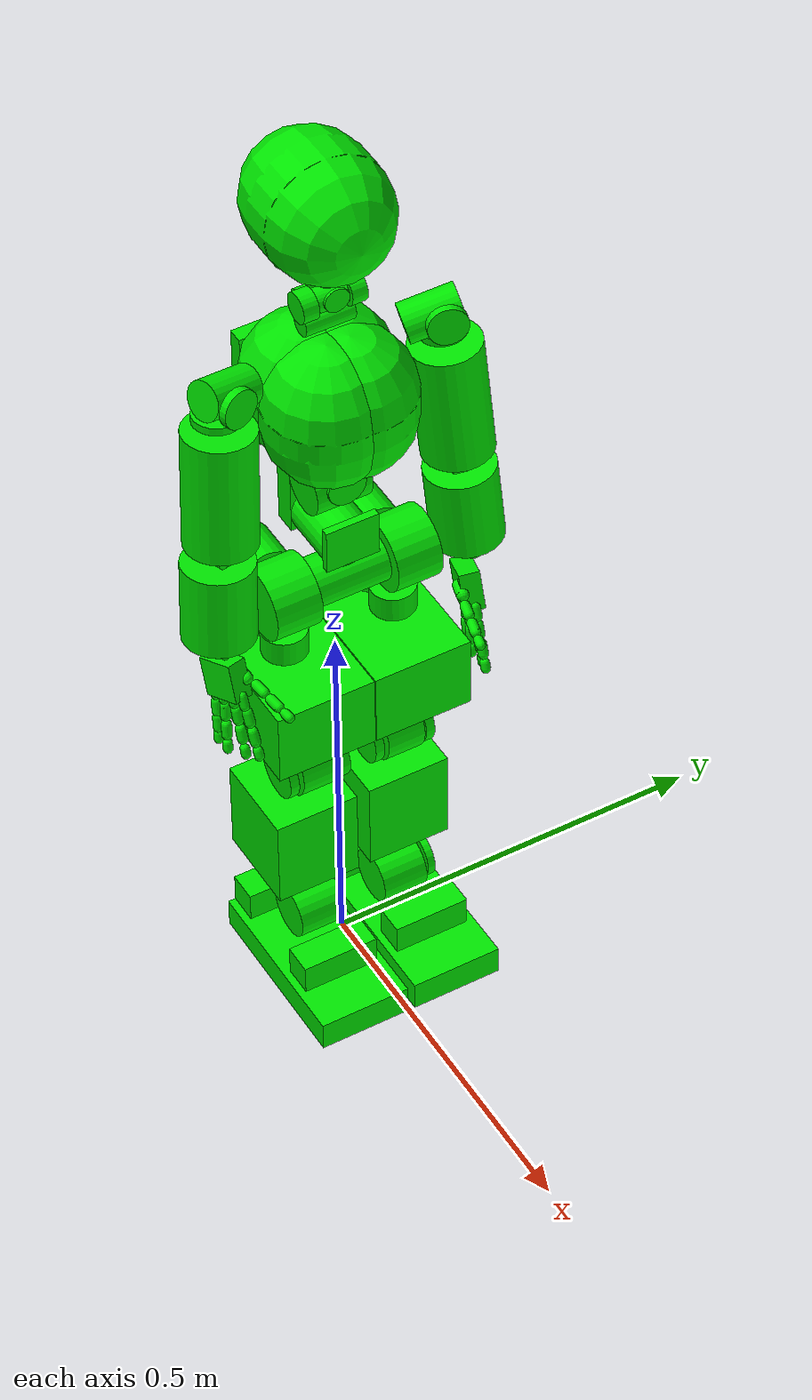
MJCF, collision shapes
<?xml version="1.0" ?>
<mujoco model="iCub">
	<compiler meshdir="iCub/meshes" texturedir="iCub/textures" angle="radian" autolimits="true" />
	<default>
		<default class="iCub_visual">
			<geom contype="0" conaffinity="0"/>
		</default>
		<default class="iCub_collision">
			<geom rgba="0.9 0.9 0.9 1.0" contype="0" conaffinity="0"/>
		</default>
		<default class="iCub_primitive_collision">
			<geom rgba="0.0 0.9 0.0 0.5"/>
		</default>
	</default>
	<asset>
		<mesh name="sim_icub3_root_link_prt_0_0010000000474974513_0_0010000000474974513_0_0010000000474974513" file="stl/sim_icub3_root_link_prt.stl" scale="0.0010000000474974513 0.0010000000474974513 0.0010000000474974513"/>
		<mesh name="sim_icub3_r_hip_1_prt_0_0010000000474974513_0_0010000000474974513_0_0010000000474974513" file="stl/sim_icub3_r_hip_1_prt.stl" scale="0.0010000000474974513 0.0010000000474974513 0.0010000000474974513"/>
		<mesh name="sim_icub3_r_hip_3_prt_0_0010000000474974513_0_0010000000474974513_0_0010000000474974513" file="stl/sim_icub3_r_hip_3_prt.stl" scale="0.0010000000474974513 0.0010000000474974513 0.0010000000474974513"/>
		<mesh name="sim_icub3_r_hip_2_prt_0_0010000000474974513_0_0010000000474974513_0_0010000000474974513" file="stl/sim_icub3_r_hip_2_prt.stl" scale="0.0010000000474974513 0.0010000000474974513 0.0010000000474974513"/>
		<mesh name="sim_icub3_r_upper_leg_prt_0_0010000000474974513_0_0010000000474974513_0_0010000000474974513" file="stl/sim_icub3_r_upper_leg_prt.stl" scale="0.0010000000474974513 0.0010000000474974513 0.0010000000474974513"/>
		<mesh name="sim_icub3_r_lower_leg_prt_0_0010000000474974513_0_0010000000474974513_0_0010000000474974513" file="stl/sim_icub3_r_lower_leg_prt.stl" scale="0.0010000000474974513 0.0010000000474974513 0.0010000000474974513"/>
		<mesh name="sim_icub3_r_ankle_1_prt_0_0010000000474974513_0_0010000000474974513_0_0010000000474974513" file="stl/sim_icub3_r_ankle_1_prt.stl" scale="0.0010000000474974513 0.0010000000474974513 0.0010000000474974513"/>
		<mesh name="sim_icub3_r_ankle_2_prt_0_0010000000474974513_0_0010000000474974513_0_0010000000474974513" file="stl/sim_icub3_r_ankle_2_prt.stl" scale="0.0010000000474974513 0.0010000000474974513 0.0010000000474974513"/>
		<mesh name="sim_icub3_l_hip_1_prt_0_0010000000474974513_0_0010000000474974513_0_0010000000474974513" file="stl/sim_icub3_l_hip_1_prt.stl" scale="0.0010000000474974513 0.0010000000474974513 0.0010000000474974513"/>
		<mesh name="sim_icub3_l_hip_3_prt_0_0010000000474974513_0_0010000000474974513_0_0010000000474974513" file="stl/sim_icub3_l_hip_3_prt.stl" scale="0.0010000000474974513 0.0010000000474974513 0.0010000000474974513"/>
		<mesh name="sim_icub3_l_hip_2_prt_0_0010000000474974513_0_0010000000474974513_0_0010000000474974513" file="stl/sim_icub3_l_hip_2_prt.stl" scale="0.0010000000474974513 0.0010000000474974513 0.0010000000474974513"/>
		<mesh name="sim_icub3_l_upper_leg_prt_0_0010000000474974513_0_0010000000474974513_0_0010000000474974513" file="stl/sim_icub3_l_upper_leg_prt.stl" scale="0.0010000000474974513 0.0010000000474974513 0.0010000000474974513"/>
		<mesh name="sim_icub3_l_lower_leg_prt_0_0010000000474974513_0_0010000000474974513_0_0010000000474974513" file="stl/sim_icub3_l_lower_leg_prt.stl" scale="0.0010000000474974513 0.0010000000474974513 0.0010000000474974513"/>
		<mesh name="sim_icub3_l_ankle_1_prt_0_0010000000474974513_0_0010000000474974513_0_0010000000474974513" file="stl/sim_icub3_l_ankle_1_prt.stl" scale="0.0010000000474974513 0.0010000000474974513 0.0010000000474974513"/>
		<mesh name="sim_icub3_l_ankle_2_prt_0_0010000000474974513_0_0010000000474974513_0_0010000000474974513" file="stl/sim_icub3_l_ankle_2_prt.stl" scale="0.0010000000474974513 0.0010000000474974513 0.0010000000474974513"/>
		<mesh name="sim_icub3_torso_1_prt_0_0010000000474974513_0_0010000000474974513_0_0010000000474974513" file="stl/sim_icub3_torso_1_prt.stl" scale="0.0010000000474974513 0.0010000000474974513 0.0010000000474974513"/>
		<mesh name="sim_icub3_torso_2_prt_0_0010000000474974513_0_0010000000474974513_0_0010000000474974513" file="stl/sim_icub3_torso_2_prt.stl" scale="0.0010000000474974513 0.0010000000474974513 0.0010000000474974513"/>
		<mesh name="sim_head_neck_1_prt_0_0010000000474974513_0_0010000000474974513_0_0010000000474974513" file="stl/sim_head_neck_1_prt.stl" scale="0.0010000000474974513 0.0010000000474974513 0.0010000000474974513"/>
		<mesh name="sim_icub3_chest_prt_0_0010000000474974513_0_0010000000474974513_0_0010000000474974513" file="stl/sim_icub3_chest_prt.stl" scale="0.0010000000474974513 0.0010000000474974513 0.0010000000474974513"/>
		<mesh name="sim_head_neck_2_prt_0_0010000000474974513_0_0010000000474974513_0_0010000000474974513" file="stl/sim_head_neck_2_prt.stl" scale="0.0010000000474974513 0.0010000000474974513 0.0010000000474974513"/>
		<mesh name="sim_head_neck_3_prt_0_0010000000474974513_0_0010000000474974513_0_0010000000474974513" file="stl/sim_head_neck_3_prt.stl" scale="0.0010000000474974513 0.0010000000474974513 0.0010000000474974513"/>
		<mesh name="sim_head_head_prt_0_0010000000474974513_0_0010000000474974513_0_0010000000474974513" file="stl/sim_head_head_prt.stl" scale="0.0010000000474974513 0.0010000000474974513 0.0010000000474974513"/>
		<mesh name="sim_icub3_r_shoulder_1_prt_0_0010000000474974513_0_0010000000474974513_0_0010000000474974513" file="stl/sim_icub3_r_shoulder_1_prt.stl" scale="0.0010000000474974513 0.0010000000474974513 0.0010000000474974513"/>
		<mesh name="sim_icub3_r_shoulder_3_prt_0_0010000000474974513_0_0010000000474974513_0_0010000000474974513" file="stl/sim_icub3_r_shoulder_3_prt.stl" scale="0.0010000000474974513 0.0010000000474974513 0.0010000000474974513"/>
		<mesh name="sim_icub3_r_shoulder_2_prt_0_0010000000474974513_0_0010000000474974513_0_0010000000474974513" file="stl/sim_icub3_r_shoulder_2_prt.stl" scale="0.0010000000474974513 0.0010000000474974513 0.0010000000474974513"/>
		<mesh name="sim_icub3_r_upperarm_prt_0_0010000000474974513_0_0010000000474974513_0_0010000000474974513" file="stl/sim_icub3_r_upperarm_prt.stl" scale="0.0010000000474974513 0.0010000000474974513 0.0010000000474974513"/>
		<mesh name="sim_icub3_r_elbow_1_prt_0_0010000000474974513_0_0010000000474974513_0_0010000000474974513" file="stl/sim_icub3_r_elbow_1_prt.stl" scale="0.0010000000474974513 0.0010000000474974513 0.0010000000474974513"/>
		<mesh name="sim_icub3_r_forearm_prt_0_0010000000474974513_0_0010000000474974513_0_0010000000474974513" file="stl/sim_icub3_r_forearm_prt.stl" scale="0.0010000000474974513 0.0010000000474974513 0.0010000000474974513"/>
		<mesh name="sim_icub3_r_wrist_1_prt_0_0010000000474974513_0_0010000000474974513_0_0010000000474974513" file="stl/sim_icub3_r_wrist_1_prt.stl" scale="0.0010000000474974513 0.0010000000474974513 0.0010000000474974513"/>
		<mesh name="col_RightHandPalm" file="stl/col_RightHandPalm.stl" scale="1.0 1.0 1.0"/>
		<mesh name="col_RightThumb0" file="stl/col_RightThumb0.stl" scale="1.0 1.0 1.0"/>
		<mesh name="col_RightThumb1" file="stl/col_RightThumb1.stl" scale="1.0 1.0 1.0"/>
		<mesh name="col_RightThumb2" file="stl/col_RightThumb2.stl" scale="1.0 1.0 1.0"/>
		<mesh name="col_RightThumb3" file="stl/col_RightThumb3.stl" scale="1.0 1.0 1.0"/>
		<mesh name="col_RightIndex0" file="stl/col_RightIndex0.stl" scale="1.0 1.0 1.0"/>
		<mesh name="col_RightIndex1" file="stl/col_RightIndex1.stl" scale="1.0 1.0 1.0"/>
		<mesh name="col_RightIndex2" file="stl/col_RightIndex2.stl" scale="1.0 1.0 1.0"/>
		<mesh name="col_RightIndex3" file="stl/col_RightIndex3.stl" scale="1.0 1.0 1.0"/>
		<mesh name="col_RightMiddle0" file="stl/col_RightMiddle0.stl" scale="1.0 1.0 1.0"/>
		<mesh name="col_RightMiddle1" file="stl/col_RightMiddle1.stl" scale="1.0 1.0 1.0"/>
		<mesh name="col_RightMiddle2" file="stl/col_RightMiddle2.stl" scale="1.0 1.0 1.0"/>
		<mesh name="col_RightMiddle3" file="stl/col_RightMiddle3.stl" scale="1.0 1.0 1.0"/>
		<mesh name="col_RightRing0" file="stl/col_RightRing0.stl" scale="1.0 1.0 1.0"/>
		<mesh name="col_RightRing1" file="stl/col_RightRing1.stl" scale="1.0 1.0 1.0"/>
		<mesh name="col_RightRing2" file="stl/col_RightRing2.stl" scale="1.0 1.0 1.0"/>
		<mesh name="col_RightRing3" file="stl/col_RightRing3.stl" scale="1.0 1.0 1.0"/>
		<mesh name="col_RightLittle0" file="stl/col_RightLittle0.stl" scale="1.0 1.0 1.0"/>
		<mesh name="col_RightLittle1" file="stl/col_RightLittle1.stl" scale="1.0 1.0 1.0"/>
		<mesh name="col_RightLittle2" file="stl/col_RightLittle2.stl" scale="1.0 1.0 1.0"/>
		<mesh name="col_RightLittle3" file="stl/col_RightLittle3.stl" scale="1.0 1.0 1.0"/>
		<mesh name="sim_icub3_l_shoulder_1_prt_0_0010000000474974513_0_0010000000474974513_0_0010000000474974513" file="stl/sim_icub3_l_shoulder_1_prt.stl" scale="0.0010000000474974513 0.0010000000474974513 0.0010000000474974513"/>
		<mesh name="sim_icub3_l_shoulder_3_prt_0_0010000000474974513_0_0010000000474974513_0_0010000000474974513" file="stl/sim_icub3_l_shoulder_3_prt.stl" scale="0.0010000000474974513 0.0010000000474974513 0.0010000000474974513"/>
		<mesh name="sim_icub3_l_shoulder_2_prt_0_0010000000474974513_0_0010000000474974513_0_0010000000474974513" file="stl/sim_icub3_l_shoulder_2_prt.stl" scale="0.0010000000474974513 0.0010000000474974513 0.0010000000474974513"/>
		<mesh name="sim_icub3_l_upperarm_prt_0_0010000000474974513_0_0010000000474974513_0_0010000000474974513" file="stl/sim_icub3_l_upperarm_prt.stl" scale="0.0010000000474974513 0.0010000000474974513 0.0010000000474974513"/>
		<mesh name="sim_icub3_l_elbow_1_prt_0_0010000000474974513_0_0010000000474974513_0_0010000000474974513" file="stl/sim_icub3_l_elbow_1_prt.stl" scale="0.0010000000474974513 0.0010000000474974513 0.0010000000474974513"/>
		<mesh name="sim_icub3_l_forearm_prt_0_0010000000474974513_0_0010000000474974513_0_0010000000474974513" file="stl/sim_icub3_l_forearm_prt.stl" scale="0.0010000000474974513 0.0010000000474974513 0.0010000000474974513"/>
		<mesh name="sim_icub3_l_wrist_1_prt_0_0010000000474974513_0_0010000000474974513_0_0010000000474974513" file="stl/sim_icub3_l_wrist_1_prt.stl" scale="0.0010000000474974513 0.0010000000474974513 0.0010000000474974513"/>
		<mesh name="col_LeftHandPalm" file="stl/col_LeftHandPalm.stl" scale="1.0 1.0 1.0"/>
		<mesh name="col_LeftThumb0" file="stl/col_LeftThumb0.stl" scale="1.0 1.0 1.0"/>
		<mesh name="col_LeftThumb1" file="stl/col_LeftThumb1.stl" scale="1.0 1.0 1.0"/>
		<mesh name="col_LeftThumb2" file="stl/col_LeftThumb2.stl" scale="1.0 1.0 1.0"/>
		<mesh name="col_LeftThumb3" file="stl/col_LeftThumb3.stl" scale="1.0 1.0 1.0"/>
		<mesh name="col_LeftIndex0" file="stl/col_LeftIndex0.stl" scale="1.0 1.0 1.0"/>
		<mesh name="col_LeftIndex1" file="stl/col_LeftIndex1.stl" scale="1.0 1.0 1.0"/>
		<mesh name="col_LeftIndex2" file="stl/col_LeftIndex2.stl" scale="1.0 1.0 1.0"/>
		<mesh name="col_LeftIndex3" file="stl/col_LeftIndex3.stl" scale="1.0 1.0 1.0"/>
		<mesh name="col_LeftMiddle0" file="stl/col_LeftMiddle0.stl" scale="1.0 1.0 1.0"/>
		<mesh name="col_LeftMiddle1" file="stl/col_LeftMiddle1.stl" scale="1.0 1.0 1.0"/>
		<mesh name="col_LeftMiddle2" file="stl/col_LeftMiddle2.stl" scale="1.0 1.0 1.0"/>
		<mesh name="col_LeftMiddle3" file="stl/col_LeftMiddle3.stl" scale="1.0 1.0 1.0"/>
		<mesh name="col_LeftRing0" file="stl/col_LeftRing0.stl" scale="1.0 1.0 1.0"/>
		<mesh name="col_LeftRing1" file="stl/col_LeftRing1.stl" scale="1.0 1.0 1.0"/>
		<mesh name="col_LeftRing2" file="stl/col_LeftRing2.stl" scale="1.0 1.0 1.0"/>
		<mesh name="col_LeftRing3" file="stl/col_LeftRing3.stl" scale="1.0 1.0 1.0"/>
		<mesh name="col_LeftLittle0" file="stl/col_LeftLittle0.stl" scale="1.0 1.0 1.0"/>
		<mesh name="full_LeftLittle1" file="stl/full_LeftLittle1.stl" scale="1.0 1.0 1.0"/>
		<mesh name="col_LeftLittle2" file="stl/col_LeftLittle2.stl" scale="1.0 1.0 1.0"/>
		<mesh name="col_LeftLittle3" file="stl/col_LeftLittle3.stl" scale="1.0 1.0 1.0"/>
	</asset>
	<worldbody>
		<body name="iCub" pos="0.0 0.0 0.0" quat="1.0 0.0 0.0 0.0">
			<body name="base_footprint" pos="0.0 0.0 0.0" quat="1.0 0.0 0.0 0.0">
				<inertial mass="1.0" pos="0.0 0.0 0.0" quat="1.0 0.0 0.0 0.0" diaginertia="0.009999999776482582 0.009999999776482582 0.009999999776482582"/>
		 		<body name="root_link" pos="0.0 0.0 0.6349999904632568" quat="1.0 0.0 0.0 0.0">
					<inertial mass="2.5750999450683594" pos="0.003550600027665496 -0.00014959200052544475 0.024519000202417374" quat="0.728122353553772 -0.00027842342387884855 -0.6854282021522522 0.005090041551738977" diaginertia="0.0025303466245532036 0.004051563795655966 0.004473471082746983"/>
					<geom name="SM_root_link_collision_mesh_0" type="mesh" pos="0.0 0.0 0.3138580024242401" quat="0.7071067690849304 0.0 0.0 -0.7071067690849304" mesh="sim_icub3_root_link_prt_0_0010000000474974513_0_0010000000474974513_0_0010000000474974513" class="iCub_collision"/>
					<geom name="SM_root_link_collision_0" type="cylinder" pos="0.002 0.0 0.06" quat="0.7071067690849304 0.0 0.7071067690849304 0.0" size="0.035 0.037" class="iCub_primitive_collision"/>
					<geom name="SM_root_link_collision_1" type="cylinder" pos="0.02 0.0 0.0" quat="0.7071067690849304 0.7071067690849304 0.0 0.0" size="0.031 0.05" class="iCub_primitive_collision"/>
					<body name="l_hip_1" pos="0.02160000056028366 0.040449999272823334 0.0" quat="1.0 0.0 0.0 0.0">
						<inertial mass="2.1084611415863037" pos="-0.002203499898314476 0.028797699138522148 -0.000493000028654933" quat="-0.7037772536277771 0.7078083753585815 0.017694594338536263 0.05823896452784538" diaginertia="0.0019451569532975554 0.0021027938928455114 0.002495991298928857"/>
						<geom name="SM_l_hip_1_collision_mesh_0" type="mesh" pos="-0.02160000056028366 -0.040449999272823334 0.3138580024242401" quat="0.7071067690849304 0.0 0.0 -0.7071067690849304" mesh="sim_icub3_l_hip_1_prt_0_0010000000474974513_0_0010000000474974513_0_0010000000474974513" class="iCub_collision"/>
						<geom name="SM_l_hip_1_collision_0" type="cylinder" pos="0.0 0.04 0.0" quat="0.7071067690849304 0.7071067690849304 0.0 0.0" size="0.046 0.03" class="iCub_primitive_collision"/>
						<joint name="l_hip_pitch" type="hinge" pos="0.0 0.0 0.0" range="-0.7853981852531433 2.0071287155151367" axis="0.0 -1.0 0.0"/>
						<body name="l_hip_2" pos="-0.04724999889731407 0.03310000151395798 -0.008999999612569809" quat="1.0 0.0 0.0 0.0">
							<inertial mass="1.7812706232070923" pos="-0.005948599893599749 8.05000017862767e-05 -0.036653000861406326" quat="0.655105471611023 -0.65507972240448 -0.26562339067459106 -0.26674243807792664" diaginertia="0.0019694678485393524 0.0040740203112363815 0.005016930866986513"/>
							<geom name="SM_l_hip_2_collision_mesh_0" type="mesh" pos="0.02565000019967556 -0.07355000078678131 0.3228580057621002" quat="0.7071067690849304 0.0 0.0 -0.7071067690849304" mesh="sim_icub3_l_hip_2_prt_0_0010000000474974513_0_0010000000474974513_0_0010000000474974513" class="iCub_collision"/>
							<geom name="SM_l_hip_2_collision_0" type="cylinder" pos="-0.028 0.0 0.0" quat="0.7071067690849304 0.0 -0.7071067690849304 0.0" size="0.035 0.03" class="iCub_primitive_collision"/>
							<geom name="SM_l_hip_2_collision_1" type="cylinder" pos="-0.028 0.0 -0.065" quat="0.7071067690849304 0.0 -0.7071067690849304 0.0" size="0.031 0.03" class="iCub_primitive_collision"/>
							<geom name="SM_l_hip_2_collision_2" type="cylinder" pos="0.037 0.0 -0.073" size="0.029 0.017" class="iCub_primitive_collision"/>
							<joint name="l_hip_roll" type="hinge" pos="0.0 0.0 0.0" range="-0.1745329201221466 2.0071287155151367" axis="1.0 0.0 0.0"/>
							<body name="l_hip_3" pos="0.03669999912381172 0.0 -0.08969999849796295" quat="1.0 0.0 0.0 0.0">
								<inertial mass="2.169151544570923" pos="0.002293400000780821 -0.012390400283038616 -0.03849299997091293" quat="-0.5509653091430664 -0.3568524718284607 -0.4141695201396942 0.6305213570594788" diaginertia="0.003588105086237192 0.0036453946959227324 0.003943108022212982"/>
								<geom name="SM_l_hip_3_collision_mesh_0" type="mesh" pos="-0.011049999855458736 -0.07355000078678131 0.412557989358902" quat="0.7071067690849304 0.0 0.0 -0.7071067690849304" mesh="sim_icub3_l_hip_3_prt_0_0010000000474974513_0_0010000000474974513_0_0010000000474974513" class="iCub_collision"/>
								<geom name="SM_l_hip_3_collision_0" type="box" pos="0.005 -0.008 -0.07" size="0.08 0.065 0.05" class="iCub_primitive_collision"/>
								<body name="l_upper_leg" pos="0.0 -0.014999999664723873 -0.07090000063180923" quat="1.0 0.0 0.0 0.0">
									<inertial mass="0.9682644605636597" pos="0.006410100031644106 0.004499500151723623 -0.05761399865150452" quat="-0.07698403298854828 -0.6447001695632935 0.07907674461603165 0.7564271688461304" diaginertia="0.001010193140245974 0.002193399937823415 0.0026930803433060646"/>
									<geom name="SM_l_upper_leg_collision_mesh_0" type="mesh" pos="-0.011049999855458736 -0.05855000019073486 0.483458012342453" quat="0.7071067690849304 0.0 0.0 -0.7071067690849304" mesh="sim_icub3_l_upper_leg_prt_0_0010000000474974513_0_0010000000474974513_0_0010000000474974513" class="iCub_collision"/>
									<geom name="SM_l_upper_leg_collision_0" type="cylinder" pos="0.018 -0.035 -0.11" quat="0.7071067690849304 -0.7071067690849304 0.0 0.0" size="0.035 0.006" class="iCub_primitive_collision"/>
									<geom name="SM_l_upper_leg_collision_1" type="cylinder" pos="0.018 0.035 -0.11" quat="0.7071067690849304 -0.7071067690849304 0.0 0.0" size="0.035 0.006" class="iCub_primitive_collision"/>
									<joint name="l_hip_yaw" type="hinge" pos="0.0 0.0 0.0" range="-1.3962633609771729 1.3962633609771729" axis="0.0 0.0 1.0"/>
									<body name="l_lower_leg" pos="0.014999999664723873 0.024900000542402267 -0.10620000213384628" quat="1.0 0.0 0.0 0.0">
										<inertial mass="5.06304931640625" pos="-0.012714199721813202 -0.02260739915072918 -0.1281760036945343" quat="0.4939037561416626 0.5054680109024048 -0.4932064712047577 0.5072559118270874" diaginertia="0.005671148654073477 0.05430392175912857 0.056787341833114624"/>
										<geom name="SM_l_lower_leg_collision_mesh_0" type="mesh" pos="-0.02604999952018261 -0.08344999700784683 0.5896580219268799" quat="0.7071067690849304 0.0 0.0 -0.7071067690849304" mesh="sim_icub3_l_lower_leg_prt_0_0010000000474974513_0_0010000000474974513_0_0010000000474974513" class="iCub_collision"/>
										<geom name="SM_l_lower_leg_collision_0" type="cylinder" pos="0.0 -0.025 0.0" quat="0.7071067690849304 -0.7071067690849304 0.0 0.0" size="0.042 0.025" class="iCub_primitive_collision"/>
										<geom name="SM_l_lower_leg_collision_1" type="box" pos="-0.025 -0.02 -0.13" size="0.06 0.055 0.063" class="iCub_primitive_collision"/>
										<geom name="SM_l_lower_leg_collision_2" type="cylinder" pos="0.0 -0.025 -0.26" quat="0.7071067690849304 -0.7071067690849304 0.0 0.0" size="0.035 0.03" class="iCub_primitive_collision"/>
										<joint name="l_knee" type="hinge" pos="0.0 0.0 0.0" range="-1.2217304706573486 0.0872664600610733" axis="0.0 -1.0 0.0"/>
										<body name="l_ankle_1" pos="0.0 -0.0005000000237487257 -0.2559889853000641" quat="1.0 0.0 0.0 0.0">
											<inertial mass="0.3461768925189972" pos="-0.005967800039798021 -0.0010992999887093902 -0.01576099917292595" quat="-0.4897749423980713 0.14573980867862701 0.3892935812473297 0.7663751840591431" diaginertia="0.009920657612383366 0.01002234686166048 0.010056995786726475"/>
											<geom name="SM_l_ankle_1_collision_mesh_0" type="mesh" pos="-0.02604999952018261 -0.08295000344514847 0.8456469774246216" quat="0.7071067690849304 0.0 0.0 -0.7071067690849304" mesh="sim_icub3_l_ankle_1_prt_0_0010000000474974513_0_0010000000474974513_0_0010000000474974513" class="iCub_collision"/>
											<geom name="SM_l_ankle_1_collision_0" type="cylinder" pos="0.0 0.015 0.0" quat="0.7071067690849304 -0.7071067690849304 0.0 0.0" size="0.03 0.005" class="iCub_primitive_collision"/>
											<joint name="l_ankle_pitch" type="hinge" pos="0.0 0.0 0.0" range="-0.7853981852531433 0.7853981852531433" axis="0.0 1.0 0.0"/>
											<body name="l_ankle_2" pos="-0.05274999886751175 -0.018200000748038292 -0.03500000014901161" quat="1.0 0.0 0.0 0.0">
												<inertial mass="1.0115336179733276" pos="0.042978398501873016 -5.850000161444768e-05 -0.025988999754190445" quat="0.001642780378460884 0.9238754510879517 0.0024752714671194553 0.3826817572116852" diaginertia="0.009209319949150085 0.010000025853514671 0.01079065352678299"/>
												<geom name="SM_l_ankle_2_collision_mesh_0" type="mesh" pos="0.02669999934732914 -0.06475000083446503 0.8806470036506653" quat="0.7071067690849304 0.0 0.0 -0.7071067690849304" mesh="sim_icub3_l_ankle_2_prt_0_0010000000474974513_0_0010000000474974513_0_0010000000474974513" class="iCub_collision"/>
												<geom name="SM_l_ankle_2_collision_0" type="box" pos="0.12 0.0 0.0" size="0.02 0.05 0.02" class="iCub_primitive_collision"/>
												<geom name="SM_l_ankle_2_collision_1" type="box" pos="-0.02 0.0 0.0" size="0.02 0.05 0.02" class="iCub_primitive_collision"/>
												<geom name="SM_l_ankle_2_collision_2" type="box" pos="0.08 0.0 -0.04" size="0.12 0.06 0.02" class="iCub_primitive_collision"/>
												<joint name="l_ankle_roll" type="hinge" pos="0.0 0.0 0.0" range="-0.4363323152065277 0.4363323152065277" axis="1.0 0.0 0.0"/>
												<body name="l_foot_rear" pos="0.01600000075995922 0.0 -0.0658000037074089" quat="1.0 0.0 0.0 0.0">
													<inertial mass="0.17459742724895477" pos="0.0005056000081822276 3.35000004270114e-05 0.0036589999217540026" quat="0.06000586599111557 0.9063477516174316 -0.18603336811065674 0.3745993375778198" diaginertia="0.009991241618990898 0.010000264272093773 0.01000849436968565"/>
													<geom name="SM_l_foot_rear_collision_mesh_0" type="box" pos="0.0 0.0 0.003000000026077032" quat="1.0 0.0 0.0 0.0" size="0.05849999934434891 0.05000000074505806 0.003000000026077032" class="iCub_collision"/>
													<geom name="SM_l_foot_rear_collision_0" type="box" pos="0.0 0.0 0.003000000026077032" quat="1.0 0.0 0.0 0.0" size="0.05849999934434891 0.05000000074505806 0.003000000026077032" class="iCub_primitive_collision"/>
													<body name="l_sole" pos="0.05962999910116196 0.0 0.0" quat="1.0 0.0 0.0 0.0">
													</body>
												</body>
												<body name="l_foot_front" pos="0.1352500021457672 0.0 -0.0658000037074089" quat="1.0 0.0 0.0 0.0">
													<inertial mass="0.1750381588935852" pos="7.699999696342275e-05 -3.989999822806567e-05 0.0042570000514388084" quat="0.001644851523451507 -0.3826756179332733 0.006170690059661865 0.9238606691360474" diaginertia="0.009965805336833 0.009999994188547134 0.010034199804067612"/>
													<geom name="SM_l_foot_front_collision_mesh_0" type="box" pos="0.0 0.0 0.003000000026077032" quat="1.0 0.0 0.0 0.0" size="0.05849999934434891 0.05000000074505806 0.003000000026077032" class="iCub_collision"/>
													<geom name="SM_l_foot_front_collision_0" type="box" pos="0.0 0.0 0.003000000026077032" quat="1.0 0.0 0.0 0.0" size="0.05849999934434891 0.05000000074505806 0.003000000026077032" class="iCub_primitive_collision"/>
												</body>
											</body>
										</body>
									</body>
								</body>
							</body>
						</body>
					</body>
					<body name="torso_1" pos="0.0 0.0 0.060499999672174454" quat="1.0 0.0 0.0 0.0">
						<inertial mass="1.7142624855041504" pos="-0.007526319939643145 0.0006843130104243755 0.05308400094509125" quat="-0.38470175862312317 0.3800213932991028 0.5943055748939514 0.5953059792518616" diaginertia="0.0019013717537745833 0.002717773662880063 0.0033514495007693768"/>
						<geom name="SM_torso_1_collision_mesh_0" type="mesh" pos="0.0 0.0 0.25335800647735596" quat="0.7071067690849304 0.0 0.0 -0.7071067690849304" mesh="sim_icub3_torso_1_prt_0_0010000000474974513_0_0010000000474974513_0_0010000000474974513" class="iCub_collision"/>
						<geom name="SM_torso_1_collision_0" type="cylinder" pos="0.0 0.0 0.073" quat="0.7071067690849304 -0.7071067690849304 0.0 0.0" size="0.035 0.0365" class="iCub_primitive_collision"/>
						<geom name="SM_torso_1_collision_1" type="box" pos="-0.05 0.0 0.03" size="0.015 0.035 0.055" class="iCub_primitive_collision"/>
						<geom name="SM_torso_1_collision_2" type="box" pos="0.045 0.0 0.008" size="0.005 0.035 0.03" class="iCub_primitive_collision"/>
						<joint name="torso_roll" type="hinge" pos="0.0 0.0 0.0" range="-0.40142571926116943 0.40142571926116943" axis="-1.0 0.0 0.0"/>
						<body name="torso_2" pos="0.0 0.0 0.07249999791383743" quat="1.0 0.0 0.0 0.0">
							<inertial mass="1.3746730089187622" pos="0.0006802239804528654 0.0015533999539911747 0.0511850006878376" quat="0.7084464430809021 -0.06150245666503906 -0.6999640464782715 0.06611666828393936" diaginertia="0.0015269903233274817 0.002160861389711499 0.002710498170927167"/>
							<geom name="SM_torso_2_collision_mesh_0" type="mesh" pos="0.0 0.0 0.18085800111293793" quat="0.7071067690849304 0.0 0.0 -0.7071067690849304" mesh="sim_icub3_torso_2_prt_0_0010000000474974513_0_0010000000474974513_0_0010000000474974513" class="iCub_collision"/>
							<geom name="SM_torso_2_collision_0" type="cylinder" pos="0.038 0.0 0.015" quat="0.7071067690849304 0.0 -0.7071067690849304 0.0" size="0.025 0.002" class="iCub_primitive_collision"/>
							<joint name="torso_pitch" type="hinge" pos="0.0 0.0 0.0" range="-0.3141592741012573 0.7853981852531433" axis="0.0 1.0 0.0"/>
							<body name="chest" pos="0.0 0.0 0.06447000056505203" quat="1.0 0.0 0.0 0.0">
								<inertial mass="7.523099899291992" pos="-0.005974330008029938 -7.260410347953439e-05 0.06416629999876022" quat="0.571567177772522 0.6059904098510742 0.3924311399459839 -0.38997989892959595" diaginertia="0.028819739818572998 0.033708710223436356 0.03386033698916435"/>
								<geom name="SM_chest_collision_mesh_0" type="mesh" pos="0.0 0.0 0.1163880005478859" quat="0.7071067690849304 0.0 0.0 -0.7071067690849304" mesh="sim_icub3_chest_prt_0_0010000000474974513_0_0010000000474974513_0_0010000000474974513" class="iCub_collision"/>
								<geom name="SM_chest_collision_0" type="capsule" pos="-0.025 0.015 0.068" size="0.08 0.015" class="iCub_primitive_collision"/>
								<geom name="SM_chest_collision_1" type="capsule" pos="-0.025 -0.015 0.068" size="0.08 0.015" class="iCub_primitive_collision"/>
								<geom name="SM_chest_collision_2" type="capsule" pos="0.025 0.015 0.068" size="0.08 0.015" class="iCub_primitive_collision"/>
								<geom name="SM_chest_collision_3" type="capsule" pos="0.025 -0.015 0.068" size="0.08 0.015" class="iCub_primitive_collision"/>
								<geom name="SM_chest_collision_4" type="box" pos="-0.09 0.0 0.03" size="0.01 0.07 0.085" class="iCub_primitive_collision"/>
								<joint name="torso_yaw" type="hinge" pos="0.0 0.0 -1.3877787807814457e-17" range="-0.7504915595054626 0.7504915595054626" axis="0.0 0.0 -1.0"/>
								<body name="chest_rgb_frame" pos="0.08941149711608887 -0.011500000022351742 0.09929949790239334" quat="0.5 -0.5 0.5 -0.5">
								</body>
								<body name="r_shoulder_1" pos="-0.02083509974181652 -0.03974229842424393 0.10520289838314056" quat="0.9835063815116882 -0.12521222233772278 -0.01648440770804882 0.129481241106987">
									<inertial mass="0.7869700193405151" pos="0.00016744811728131026 -0.08721740543842316 0.0004507343110162765" quat="0.7457836270332336 0.584801435470581 -0.00941787101328373 -0.3189442455768585" diaginertia="0.009740661829710007 0.010040726512670517 0.010218611918389797"/>
									<geom name="SM_r_shoulder_1_collision_mesh_0" type="mesh" pos="0.030411234125494957 0.02914046309888363 0.019095774739980698" quat="-0.6038869619369507 -0.07688217610120773 -0.10019464790821075 0.7870010733604431" mesh="sim_icub3_r_shoulder_1_prt_0_0010000000474974513_0_0010000000474974513_0_0010000000474974513" class="iCub_collision"/>
									<geom name="SM_r_shoulder_1_collision_0" type="cylinder" pos="0.0 -0.1 0.0" quat="0.7071067690849304 -0.7071067690849304 0.0 0.0" size="0.025 0.035" class="iCub_primitive_collision"/>
									<joint name="r_shoulder_pitch" type="hinge" pos="0.0 0.0 1.3877787807814457e-17" range="-0.3490658402442932 3.054326295852661" axis="1.4990443730766856e-07 -1.0 -1.456618718975733e-07"/>
									<body name="r_shoulder_2" pos="0.007489008363336325 -0.11150041222572327 0.00040278589585796" quat="0.99583500623703 0.08712433278560638 -0.026768436655402184 0.0023416290059685707">
										<inertial mass="0.424919992685318" pos="0.005108925048261881 -0.00021262472728267312 -0.020403359085321426" quat="-0.43466272950172424 0.20708465576171875 0.0706920251250267 0.8736056685447693" diaginertia="0.009874754585325718 0.010047122836112976 0.010078122839331627"/>
										<geom name="SM_r_shoulder_2_collision_mesh_0" type="mesh" pos="0.023893259465694427 0.14064089953899384 0.017434528097510338" quat="-0.600976824760437 -0.05570726469159126 -0.11638544499874115 0.7887825965881348" mesh="sim_icub3_r_shoulder_2_prt_0_0010000000474974513_0_0010000000474974513_0_0010000000474974513" class="iCub_collision"/>
										<geom name="SM_r_shoulder_2_collision_0" type="cylinder" pos="-0.01 0.0 -0.03" size="0.03 0.005" class="iCub_primitive_collision"/>
										<geom name="SM_r_shoulder_2_collision_1" type="cylinder" pos="0.025 0.0 0.0" quat="0.7071067690849304 0.0 -0.7071067690849304 0.0" size="0.025 0.005" class="iCub_primitive_collision"/>
										<joint name="r_shoulder_roll" type="hinge" pos="7.424289277617633e-18 3.63239557692615e-17 2.3736409243990934e-17" range="0.20943951606750488 2.8448867797851562" axis="-1.0 4.2105021691440925e-08 1.983887045753363e-07"/>
										<body name="r_shoulder_3" pos="-0.006849946454167366 2.190499657217515e-07 -0.0542999804019928" quat="1.0 0.0 3.469446951953614e-18 -1.1926223897340549e-17">
											<inertial mass="0.26249998807907104" pos="-8.296442683786154e-05 -3.030926745850593e-05 -0.007966520264744759" quat="-0.21879516541957855 0.8601486682891846 -0.34936317801475525 -0.30036357045173645" diaginertia="0.009988508187234402 0.009998657740652561 0.010012834332883358"/>
											<geom name="SM_r_shoulder_3_collision_0" type="mesh" pos="0.030743205919861794 0.14064067602157593 0.07173451036214828" quat="-0.600976824760437 -0.05570726469159126 -0.11638544499874115 0.7887825965881348" mesh="sim_icub3_r_shoulder_3_prt_0_0010000000474974513_0_0010000000474974513_0_0010000000474974513" class="iCub_collision"/>
											<body name="r_upper_arm" pos="-3.469446951953614e-18 4.2183273762930185e-07 -0.022499941289424896" quat="1.0 0.0 3.469446951953614e-18 -1.1926223897340549e-17">
												<inertial mass="1.621899962425232" pos="0.0010476388270035386 -0.0025596260093152523 -0.05065314844250679" quat="0.27496689558029175 0.6602051854133606 -0.46689748764038086 0.520124077796936" diaginertia="0.0012327951844781637 0.002889610594138503 0.0029981478583067656"/>
												<geom name="SM_r_upper_arm_collision_mesh_0" type="mesh" pos="0.030743123963475227 0.1406402587890625 0.09423445165157318" quat="-0.600976824760437 -0.05570726469159126 -0.11638544499874115 0.7887825965881348" mesh="sim_icub3_r_upperarm_prt_0_0010000000474974513_0_0010000000474974513_0_0010000000474974513" class="iCub_collision"/>
												<geom name="SM_r_upper_arm_collision_0" type="cylinder" pos="0.0 0.0 -0.05" size="0.045 0.08" class="iCub_primitive_collision"/>
												<joint name="r_shoulder_yaw" type="hinge" pos="2.4537583298085294e-17 4.3083827936277555e-17 1.2062363267787996e-16" range="-0.8726646304130554 1.3962633609771729" axis="-3.7876212388709973e-08 2.805197318878072e-08 1.0"/>
												<body name="r_elbow_1" pos="0.009999931789934635 0.001499640173278749 -0.1237003356218338" quat="1.0 0.0 3.469446951953614e-18 -1.1926223897340549e-17">
													<inertial mass="0.2215700000524521" pos="-0.009961389005184174 -0.0004824674397241324 -0.014881572686135769" quat="-0.6387526392936707 0.12840628623962402 0.3282998502254486 0.6839050054550171" diaginertia="0.009975533001124859 0.010000602342188358 0.010023864917457104"/>
													<geom name="SM_r_elbow_1_collision_mesh_0" type="mesh" pos="0.020743191242218018 0.13914062082767487 0.21793478727340698" quat="-0.600976824760437 -0.05570726469159126 -0.11638544499874115 0.7887825965881348" mesh="sim_icub3_r_elbow_1_prt_0_0010000000474974513_0_0010000000474974513_0_0010000000474974513" class="iCub_collision"/>
													<geom name="SM_r_elbow_1_collision_0" type="cylinder" pos="-0.01 0.0 -0.02" quat="0.7071067690849304 -0.7071067690849304 0.0 0.0" size="0.02 0.01" class="iCub_primitive_collision"/>
													<joint name="r_elbow" type="hinge" pos="1.5342827243041825e-17 4.8768461259925727e-17 7.276389549529274e-17" range="-0.05235987901687622 1.3089969158172607" axis="2.494957698218059e-07 -1.0 -2.454089553793892e-07"/>
													<body name="r_forearm" pos="-0.014999869279563427 -0.001999649917706847 -0.055300064384937286" quat="1.0 0.0 3.469446951953614e-18 -1.1926223897340549e-17">
														<inertial mass="0.8686000108718872" pos="-0.005904319696128368 -3.491232291708002e-06 -0.030210372060537338" quat="0.5510739088058472 0.415446400642395 0.6658050417900085 -0.2835939824581146" diaginertia="0.0005981656722724438 0.0012388339964672923 0.0012617256725206971"/>
														<geom name="SM_r_forearm_collision_mesh_0" type="mesh" pos="0.03574306145310402 0.14114026725292206 0.27323484420776367" quat="-0.600976824760437 -0.05570726469159126 -0.11638544499874115 0.7887825965881348" mesh="sim_icub3_r_forearm_prt_0_0010000000474974513_0_0010000000474974513_0_0010000000474974513" class="iCub_collision"/>
														<geom name="SM_r_forearm_collision_0" type="cylinder" pos="0.0 0.0 -0.036" size="0.045 0.054" class="iCub_primitive_collision"/>
														<joint name="r_wrist_prosup" type="hinge" pos="2.042410841044892e-17 1.9499661284027006e-17 5.623888488184728e-17" range="-1.535889744758606 1.535889744758606" axis="-3.7876212388709973e-08 2.805197318878072e-08 1.0"/>
														<body name="r_wrist_1" pos="0.016299953684210777 -0.002007442992180586 -0.10750007629394531" quat="1.0 0.0 3.469446951953614e-18 -1.1926223897340549e-17">
															<inertial mass="0.03318300098180771" pos="-0.014340376481413841 0.0005016179056838155 -0.0001151262695202604" quat="-0.2627790570259094 -0.42736291885375977 0.6720929741859436 0.5446091294288635" diaginertia="0.009999112226068974 0.009999994188547134 0.010000893846154213"/>
															<geom name="SM_r_wrist_1_collision_mesh_0" type="mesh" pos="0.019443107768893242 0.14314770698547363 0.380734920501709" quat="-0.600976824760437 -0.05570726469159126 -0.11638544499874115 0.7887825965881348" mesh="sim_icub3_r_wrist_1_prt_0_0010000000474974513_0_0010000000474974513_0_0010000000474974513" class="iCub_collision"/>
															<geom name="SM_r_wrist_1_collision_0" type="cylinder" pos="-0.02 0.0 0.0" quat="0.7071067690849304 0.0 -0.7071067690849304 0.0" size="0.01 0.02" class="iCub_primitive_collision"/>
															<joint name="r_wrist_pitch" type="hinge" pos="9.872227730072362e-18 3.1374236023919743e-17 -8.167046017056151e-17" range="-1.2217304706573486 0.4363323152065277" axis="1.0 4.2105021691440925e-08 -1.983887045753363e-07"/>
															<body name="r_hand" pos="-0.016300123184919357 0.006999390199780464 0.0" quat="-7.312061383896867e-14 0.7071067690849304 7.311908240340004e-14 0.7071067690849304">
																<inertial mass="0.2570500075817108" pos="0.004771493375301361 0.006220157723873854 -0.06696908175945282" quat="0.6324418187141418 0.12631399929523468 -0.4972488284111023 -0.5803496241569519" diaginertia="0.009942249394953251 0.009974818676710129 0.010082932189106941"/>
																<geom name="SM_r_hand_collision_mesh_0" type="mesh" pos="-0.0027160674799233675 -0.0015567999798804522 -0.0024823539424687624" quat="-0.7010573744773865 0.7010573744773865 -0.09229592978954315 -0.09229592978954315" mesh="col_RightHandPalm" class="iCub_collision"/>
																<geom name="SM_r_hand_collision_0" type="box" pos="-0.04 0.005 0.01" quat="-0.7010573744773865 0.7010573744773865 -0.09229592978954315 -0.09229592978954315" size="0.025 0.025 0.013" class="iCub_primitive_collision"/>
																<joint name="r_wrist_yaw" type="hinge" pos="-7.534170295827952e-18 -2.6658087268144582e-17 -1.7189102642066309e-18" range="-0.2617993950843811 0.6108652353286743" axis="-2.494957698218059e-07 1.0 2.454089553793892e-07"/>
																<body name="r_hand_index_0" pos="-0.05255843326449394 0.005143200047314167 0.039473339915275574" quat="-0.12013258785009384 -0.11427372694015503 0.7273476123809814 -0.6659393310546875">
																	<inertial mass="0.009999999776482582" pos="0.0 0.0 0.0" quat="1.0 0.0 0.0 0.0" diaginertia="0.0010000000474974513 0.0010000000474974513 0.0010000000474974513"/>
																	<geom name="SM_r_hand_index_0_collision_mesh_0" type="mesh" pos="0.0 0.0 0.0" quat="2.609984337526221e-30 1.6155445638695877e-15 1.0 1.6155445638695877e-15" mesh="col_RightIndex0" class="iCub_collision"/>
																	<geom name="SM_r_hand_index_0_collision_0" type="capsule" pos="0.007 0.002 -0.001" quat="-7.312061383896867e-14 0.7071067690849304 7.311908240340004e-14 0.7071067690849304" size="0.006 0.007" class="iCub_primitive_collision"/>
																	<joint name="r_hand_index_0_joint" type="hinge" pos="1.2200603842427451e-17 -4.0746169203088395e-17 -3.8314294598129446e-17" range="-0.3490658402442932 0.0" axis="0.0 0.0 1.0"/>
																	<body name="r_hand_index_1" pos="0.014800000004470348 0.0017500000540167093 0.0" quat="0.7071067690849304 0.7071067690849304 3.189250438235362e-17 -4.17055795996417e-17">
																		<inertial mass="0.009999999776482582" pos="0.0 0.0 0.0" quat="1.0 0.0 0.0 0.0" diaginertia="0.0010000000474974513 0.0010000000474974513 0.0010000000474974513"/>
																		<geom name="SM_r_hand_index_1_collision_mesh_0" type="mesh" pos="0.0 0.0 0.0" quat="1.6155445638695877e-15 1.0 0.0 0.0" mesh="col_RightIndex1" class="iCub_collision"/>
																		<geom name="SM_r_hand_index_1_collision_0" type="capsule" pos="0.015 0.0 0.0" quat="-7.312061383896867e-14 0.7071067690849304 7.311908240340004e-14 0.7071067690849304" size="0.0065 0.007" class="iCub_primitive_collision"/>
																		<joint name="r_hand_index_1_joint" type="hinge" pos="-1.3139740869347693e-17 3.035666490413661e-17 1.057552729254761e-17" range="0.0 1.5707963705062866" axis="0.0 0.0 1.0"/>
																		<body name="r_hand_index_2" pos="0.02590000070631504 2.7755575615628914e-17 0.0" quat="1.0 1.0408340855860843e-17 1.3877787807814457e-17 3.469446951953614e-18">
																			<inertial mass="0.009999999776482582" pos="0.0 0.0 0.0" quat="1.0 0.0 0.0 0.0" diaginertia="0.0010000000474974513 0.0010000000474974513 0.0010000000474974513"/>
																			<geom name="SM_r_hand_index_2_collision_mesh_0" type="mesh" pos="0.0 0.0 0.0" quat="1.6155445638695877e-15 1.0 0.0 0.0" mesh="col_RightIndex2" class="iCub_collision"/>
																			<geom name="SM_r_hand_index_2_collision_0" type="capsule" pos="0.015 0.0 0.0" quat="-7.312061383896867e-14 0.7071067690849304 7.311908240340004e-14 0.7071067690849304" size="0.0065 0.007" class="iCub_primitive_collision"/>
																			<joint name="r_hand_index_2_joint" type="hinge" pos="2.799935566831564e-17 -5.223902656006751e-17 5.552864775557455e-17" range="0.0 1.5707963705062866" axis="0.0 0.0 1.0"/>
																			<body name="r_hand_index_3" pos="0.02199999988079071 2.7755575615628914e-17 0.0" quat="1.0 1.0408340855860843e-17 1.3877787807814457e-17 3.469446951953614e-18">
																				<inertial mass="0.009999999776482582" pos="0.0 0.0 0.0" quat="1.0 0.0 0.0 0.0" diaginertia="0.0010000000474974513 0.0010000000474974513 0.0010000000474974513"/>
																				<geom name="SM_r_hand_index_3_collision_mesh_0" type="mesh" pos="0.0 0.0 0.0" quat="2.609984337526221e-30 1.6155445638695877e-15 1.0 1.6155445638695877e-15" mesh="col_RightIndex3" class="iCub_collision"/>
																				<geom name="SM_r_hand_index_3_collision_0" type="capsule" pos="0.015 0.0 0.0" quat="-7.312061383896867e-14 0.7071067690849304 7.311908240340004e-14 0.7071067690849304" size="0.006 0.004" class="iCub_primitive_collision"/>
																				<joint name="r_hand_index_3_joint" type="hinge" pos="-8.915341061567957e-18 -1.8695755879549995e-17 -2.7833284271094595e-17" range="0.0 1.5707963705062866" axis="0.0 0.0 1.0"/>
																				<body name="r_hand_index_tip" pos="0.01679999940097332 -2.7755575615628914e-17 0.0" quat="0.7071067690849304 -0.7071067690849304 -6.869154637335128e-17 -4.906538932133021e-17">
																				</body>
																			</body>
																		</body>
																	</body>
																</body>
																<body name="r_hand_middle_0" pos="-0.05754045024514198 0.0060431999154388905 0.023777974769473076" quat="0.09229592978954315 0.09229592978954315 -0.7010573744773865 0.7010573744773865">
																	<inertial mass="0.009999999776482582" pos="0.0 0.0 0.0" quat="1.0 0.0 0.0 0.0" diaginertia="0.0010000000474974513 0.0010000000474974513 0.0010000000474974513"/>
																	<geom name="SM_r_hand_middle_0_collision_mesh_0" type="mesh" pos="0.0 0.0 0.0035000001080334187" quat="1.0 0.0 0.0 0.0" mesh="col_RightMiddle0" class="iCub_collision"/>
																	<geom name="SM_r_hand_middle_0_collision_0" type="capsule" pos="0.007 0.002 -0.001" quat="-7.312061383896867e-14 0.7071067690849304 7.311908240340004e-14 0.7071067690849304" size="0.006 0.007" class="iCub_primitive_collision"/>
																	<joint name="r_hand_middle_0_joint" type="hinge" pos="3.9026827977782624e-18 -2.835248238053698e-17 -1.6511623522411903e-16" range="0.0 0.3490658503988659" axis="0.0 0.0 1.0"/>
																	<body name="r_hand_middle_1" pos="0.015300000086426735 0.002199999988079071 0.0" quat="0.7071067690849304 0.7071067690849304 -1.4719616134654573e-17 5.887846453861829e-17">
																		<inertial mass="0.009999999776482582" pos="0.0 0.0 0.0" quat="1.0 0.0 0.0 0.0" diaginertia="0.0010000000474974513 0.0010000000474974513 0.0010000000474974513"/>
																		<geom name="SM_r_hand_middle_1_collision_mesh_0" type="mesh" pos="0.0 0.0 0.0" quat="1.6155445638695877e-15 1.0 0.0 0.0" mesh="col_RightMiddle1" class="iCub_collision"/>
																		<geom name="SM_r_hand_middle_1_collision_0" type="capsule" pos="0.015 0.0 0.0" quat="-7.312061383896867e-14 0.7071067690849304 7.311908240340004e-14 0.7071067690849304" size="0.0065 0.007" class="iCub_primitive_collision"/>
																		<joint name="r_hand_middle_1_joint" type="hinge" pos="6.1125851397198316e-18 -1.5268602672316217e-17 -1.2165533038816428e-17" range="0.0 1.5707963705062866" axis="0.0 0.0 1.0"/>
																		<body name="r_hand_middle_2" pos="0.025800000876188278 2.7755575615628914e-17 0.0" quat="1.0 1.5612511283791264e-17 1.3877787807814457e-17 -3.469446951953614e-18">
																			<inertial mass="0.009999999776482582" pos="0.0 0.0 0.0" quat="1.0 0.0 0.0 0.0" diaginertia="0.0010000000474974513 0.0010000000474974513 0.0010000000474974513"/>
																			<geom name="SM_r_hand_middle_2_collision_mesh_0" type="mesh" pos="0.0 0.0 0.0" quat="1.6155445638695877e-15 0.0 0.0 1.0" mesh="col_RightMiddle2" class="iCub_collision"/>
																			<geom name="SM_r_hand_middle_2_collision_0" type="capsule" pos="0.015 0.0 0.0" quat="-7.312061383896867e-14 0.7071067690849304 7.311908240340004e-14 0.7071067690849304" size="0.0065 0.007" class="iCub_primitive_collision"/>
																			<joint name="r_hand_middle_2_joint" type="hinge" pos="-1.4617530466536954e-17 -1.4615110136064624e-17 -4.875819760288517e-17" range="0.0 1.5707963705062866" axis="0.0 0.0 1.0"/>
																			<body name="r_hand_middle_3" pos="0.024000000208616257 2.7755575615628914e-17 2.7755575615628914e-17" quat="1.0 1.5612511283791264e-17 1.3877787807814457e-17 -3.469446951953614e-18">
																				<inertial mass="0.009999999776482582" pos="0.0 0.0 0.0" quat="1.0 0.0 0.0 0.0" diaginertia="0.0010000000474974513 0.0010000000474974513 0.0010000000474974513"/>
																				<geom name="SM_r_hand_middle_3_collision_mesh_0" type="mesh" pos="0.0 0.0 0.0" quat="1.6155445638695877e-15 0.0 0.0 1.0" mesh="col_RightMiddle3" class="iCub_collision"/>
																				<geom name="SM_r_hand_middle_3_collision_0" type="capsule" pos="0.015 0.0 0.0" quat="-7.312061383896867e-14 0.7071067690849304 7.311908240340004e-14 0.7071067690849304" size="0.006 0.004" class="iCub_primitive_collision"/>
																				<joint name="r_hand_middle_3_joint" type="hinge" pos="3.704806636876797e-17 -3.373227648740221e-17 1.5297853433137317e-17" range="0.0 1.5707963705062866" axis="0.0 0.0 1.0"/>
																				<body name="r_hand_middle_tip" pos="0.01679999940097332 0.0 0.0" quat="0.7071067690849304 -0.7071067690849304 5.289862368923975e-17 -2.0699461947116796e-17">
																					<inertial mass="0.0" pos="0.0 0.0 0.0" quat="1.0 0.0 0.0 0.0" diaginertia="0.0 0.0 0.0"/>
																				</body>
																			</body>
																		</body>
																	</body>
																</body>
																<body name="r_hand_ring_0" pos="-0.06069108471274376 0.0054432000033557415 0.008658226579427719" quat="0.08513370156288147 0.02448935993015766 -0.6986569166183472 0.7099514007568359">
																	<inertial mass="0.009999999776482582" pos="0.0 0.0 0.0" quat="1.0 0.0 0.0 0.0" diaginertia="0.0010000000474974513 0.0010000000474974513 0.0010000000474974513"/>
																	<geom name="SM_r_hand_ring_0_collision_mesh_0" type="mesh" pos="0.0 0.0 0.0" quat="2.609984337526221e-30 1.6155445638695877e-15 1.0 1.6155445638695877e-15" mesh="col_RightRing0" class="iCub_collision"/>
																	<geom name="SM_r_hand_ring_0_collision_0" type="capsule" pos="0.007 0.002 -0.001" quat="-7.312061383896867e-14 0.7071067690849304 7.311908240340004e-14 0.7071067690849304" size="0.006 0.007" class="iCub_primitive_collision"/>
																	<joint name="r_hand_ring_0_joint" type="hinge" pos="7.389780129642533e-18 -4.246371710082615e-17 -1.1039573630956389e-16" range="0.0 0.3490658402442932" axis="0.0 0.0 1.0"/>
																	<body name="r_hand_ring_1" pos="0.014800000004470348 0.0017500000540167093 0.0" quat="0.7071067690849304 0.7071067690849304 -1.962615539765984e-17 -1.962615539765984e-17">
																		<inertial mass="0.009999999776482582" pos="0.0 0.0 0.0" quat="1.0 0.0 0.0 0.0" diaginertia="0.0010000000474974513 0.0010000000474974513 0.0010000000474974513"/>
																		<geom name="SM_r_hand_ring_1_collision_mesh_0" type="mesh" pos="0.0 0.0 0.0" quat="1.0 0.0 0.0 0.0" mesh="col_RightRing1" class="iCub_collision"/>
																		<geom name="SM_r_hand_ring_1_collision_0" type="capsule" pos="0.015 0.0 0.0" quat="-7.312061383896867e-14 0.7071067690849304 7.311908240340004e-14 0.7071067690849304" size="0.0065 0.007" class="iCub_primitive_collision"/>
																		<joint name="r_hand_ring_1_joint" type="hinge" pos="8.122386701220535e-18 -1.1691297985930588e-17 -3.2979105378615526e-17" range="0.0 1.5707963705062866" axis="0.0 0.0 1.0"/>
																		<body name="r_hand_ring_2" pos="0.02590000070631504 0.0 0.0" quat="1.0 1.5612511283791264e-17 -6.938893903907228e-18 3.0814879110195774e-33">
																			<inertial mass="0.009999999776482582" pos="0.0 0.0 0.0" quat="1.0 0.0 0.0 0.0" diaginertia="0.0010000000474974513 0.0010000000474974513 0.0010000000474974513"/>
																			<geom name="SM_r_hand_ring_2_collision_mesh_0" type="mesh" pos="0.0 0.0 0.0" quat="1.6155445638695877e-15 1.0 0.0 0.0" mesh="col_RightRing2" class="iCub_collision"/>
																			<geom name="SM_r_hand_ring_2_collision_0" type="capsule" pos="0.015 0.0 0.0" quat="-7.312061383896867e-14 0.7071067690849304 7.311908240340004e-14 0.7071067690849304" size="0.0065 0.007" class="iCub_primitive_collision"/>
																			<joint name="r_hand_ring_2_joint" type="hinge" pos="5.019498220274895e-18 -4.960796934514763e-18 1.958390632069308e-17" range="0.0 1.5707963705062866" axis="0.0 0.0 1.0"/>
																			<body name="r_hand_ring_3" pos="0.02199999988079071 0.0 0.0" quat="1.0 1.5612511283791264e-17 -6.938893903907228e-18 3.0814879110195774e-33">
																				<inertial mass="0.009999999776482582" pos="0.0 0.0 0.0" quat="1.0 0.0 0.0 0.0" diaginertia="0.0010000000474974513 0.0010000000474974513 0.0010000000474974513"/>
																				<geom name="SM_r_hand_ring_3_collision_mesh_0" type="mesh" pos="0.0 0.0 0.0" quat="2.609984337526221e-30 1.6155445638695877e-15 1.0 1.6155445638695877e-15" mesh="col_RightRing3" class="iCub_collision"/>
																				<geom name="SM_r_hand_ring_3_collision_0" type="capsule" pos="0.015 0.0 0.0" quat="-7.312061383896867e-14 0.7071067690849304 7.311908240340004e-14 0.7071067690849304" size="0.006 0.004" class="iCub_primitive_collision"/>
																				<joint name="r_hand_ring_3_joint" type="hinge" pos="-5.019498220274895e-18 4.960796934514763e-18 -1.958390632069308e-17" range="0.0 1.5707963705062866" axis="0.0 0.0 1.0"/>
																				<body name="r_hand_ring_tip" pos="0.01679999940097332 0.0 -1.3877787807814457e-17" quat="0.7071067690849304 -0.7071067690849304 -7.237144792547308e-17 7.237144792547308e-17">
																					<inertial mass="0.0" pos="0.0 0.0 0.0" quat="1.0 0.0 0.0 0.0" diaginertia="0.0 0.0 0.0"/>
																				</body>
																			</body>
																		</body>
																	</body>
																</body>
																<body name="r_hand_little_0" pos="-0.06362900137901306 0.004443199839442968 -0.010110927745699883" quat="0.08513370156288147 0.02448935993015766 -0.6986569166183472 0.7099514007568359">
																	<inertial mass="0.009999999776482582" pos="0.0 0.0 0.0" quat="1.0 0.0 0.0 0.0" diaginertia="0.0010000000474974513 0.0010000000474974513 0.0010000000474974513"/>
																	<geom name="SM_r_hand_little_0_collision_mesh_0" type="mesh" pos="0.0 0.0 0.003800000064074993" quat="1.0 0.0 0.0 0.0" mesh="col_RightLittle0" class="iCub_collision"/>
																	<geom name="SM_r_hand_little_0_collision_0" type="capsule" pos="0.007 -0.002 -0.001" quat="-7.312061383896867e-14 0.7071067690849304 7.311908240340004e-14 0.7071067690849304" size="0.006 0.007" class="iCub_primitive_collision"/>
																	<joint name="r_hand_little_0_joint" type="hinge" pos="2.993997391133394e-18 1.906093461329623e-17 -1.9513725008801632e-17" range="0.0 0.3490658402442932" axis="0.0 0.0 1.0"/>
																	<body name="r_hand_little_1" pos="0.014800000004470348 -0.0017500000540167093 0.0" quat="0.7071067690849304 0.7071067690849304 -1.962615539765984e-17 -1.962615539765984e-17">
																		<inertial mass="0.009999999776482582" pos="0.0 0.0 0.0" quat="1.0 0.0 0.0 0.0" diaginertia="0.0010000000474974513 0.0010000000474974513 0.0010000000474974513"/>
																		<geom name="SM_r_hand_little_1_collision_mesh_0" type="mesh" pos="0.0 0.0 0.0" quat="1.6155445638695877e-15 1.0 0.0 0.0" mesh="col_RightLittle1" class="iCub_collision"/>
																		<geom name="SM_r_hand_little_1_collision_0" type="capsule" pos="0.015 0.0 0.0" quat="-7.312061383896867e-14 0.7071067690849304 7.311908240340004e-14 0.7071067690849304" size="0.0065 0.007" class="iCub_primitive_collision"/>
																		<joint name="r_hand_little_1_joint" type="hinge" pos="3.010923863930975e-17 -1.281928249736628e-16 -1.6691014181856278e-17" range="0.0 1.5707963705062866" axis="0.0 0.0 1.0"/>
																		<body name="r_hand_little_2" pos="0.021900000050663948 -5.551115123125783e-17 0.0" quat="1.0 1.5612511283791264e-17 -6.938893903907228e-18 3.0814879110195774e-33">
																			<inertial mass="0.009999999776482582" pos="0.0 0.0 0.0" quat="1.0 0.0 0.0 0.0" diaginertia="0.0010000000474974513 0.0010000000474974513 0.0010000000474974513"/>
																			<geom name="SM_r_hand_little_2_collision_mesh_0" type="mesh" pos="0.0 0.0 0.0" quat="1.6155445638695877e-15 1.0 0.0 0.0" mesh="col_RightLittle2" class="iCub_collision"/>
																			<geom name="SM_r_hand_little_2_collision_0" type="capsule" pos="0.015 0.0 0.0" quat="-7.312061383896867e-14 0.7071067690849304 7.311908240340004e-14 0.7071067690849304" size="0.0065 0.007" class="iCub_primitive_collision"/>
																			<joint name="r_hand_little_2_joint" type="hinge" pos="1.6818806193568996e-19 4.737618394010097e-17 3.7772650115584823e-17" range="0.0 1.5707963705062866" axis="0.0 0.0 1.0"/>
																			<body name="r_hand_little_3" pos="0.01899999938905239 5.551115123125783e-17 -1.3877787807814457e-17" quat="1.0 1.5612511283791264e-17 -6.938893903907228e-18 3.0814879110195774e-33">
																				<inertial mass="0.009999999776482582" pos="0.0 0.0 0.0" quat="1.0 0.0 0.0 0.0" diaginertia="0.0010000000474974513 0.0010000000474974513 0.0010000000474974513"/>
																				<geom name="SM_r_hand_little_3_collision_mesh_0" type="mesh" pos="0.0 0.0 0.0" quat="2.609984337526221e-30 1.6155445638695877e-15 1.0 1.6155445638695877e-15" mesh="col_RightLittle3" class="iCub_collision"/>
																				<geom name="SM_r_hand_little_3_collision_0" type="capsule" pos="0.015 0.0 0.0" quat="-7.312061383896867e-14 0.7071067690849304 7.311908240340004e-14 0.7071067690849304" size="0.006 0.004" class="iCub_primitive_collision"/>
																				<joint name="r_hand_little_3_joint" type="hinge" pos="-1.1888044548987551e-17 -5.1267241541550415e-17 -2.837872054956716e-17" range="0.0 1.5707963705062866" axis="0.0 0.0 1.0"/>
																				<body name="r_hand_little_tip" pos="0.01679999940097332 0.0 -2.7755575615628914e-17" quat="0.7071067690849304 -0.7071067690849304 -7.237144792547308e-17 7.237144792547308e-17">
																					<inertial mass="0.0" pos="0.0 0.0 0.0" quat="1.0 0.0 0.0 0.0" diaginertia="0.0 0.0 0.0"/>
																				</body>
																			</body>
																		</body>
																	</body>
																</body>
																<body name="r_gripper_tool_frame" pos="1.1102230246251565e-16 2.7755575615628914e-17 0.12999999523162842" quat="1.0 1.1275702593849246e-17 0.0 0.0">
																</body>
																<body name="r_hand_thumb_0" pos="-0.0318492129445076 -0.004056800156831741 0.019202696159482002" quat="0.03826058655977249 0.6148546934127808 -0.016224896535277367 0.7875446677207947">
																	<inertial mass="0.009999999776482582" pos="0.0 0.0 0.0" quat="1.0 0.0 0.0 0.0" diaginertia="0.0010000000474974513 0.0010000000474974513 0.0010000000474974513"/>
																	<geom name="SM_r_hand_thumb_0_collision_mesh_0" type="mesh" pos="0.0 0.0 0.0" quat="-7.312638043927358e-14 -0.7071067690849304 0.7071067690849304 -7.315724631987153e-14" mesh="col_RightThumb0" class="iCub_collision"/>
																	<geom name="SM_r_hand_thumb_0_collision_0" type="capsule" pos="0.007 0.003 -0.001" quat="-0.7071067690849304 0.0 0.7071067690849304 -7.315724631987153e-14" size="0.008 0.007" class="iCub_primitive_collision"/>
																	<joint name="r_hand_thumb_0_joint" type="hinge" pos="1.4951003367404032e-17 -4.4006038366323124e-17 -1.5272657842551197e-16" range="0.0 1.5707963705062866" axis="0.0 0.0 1.0"/>
																	<body name="r_hand_thumb_1" pos="0.0210999995470047 0.004900000058114529 0.0" quat="-0.7071067690849304 0.7071067690849304 3.679904033663643e-18 2.45326942470748e-18">
																		<inertial mass="0.009999999776482582" pos="0.0 0.0 0.0" quat="1.0 0.0 0.0 0.0" diaginertia="0.0010000000474974513 0.0010000000474974513 0.0010000000474974513"/>
																		<geom name="SM_r_hand_thumb_1_collision_mesh_0" type="mesh" pos="0.0 0.0 0.0" quat="1.6155445638695877e-15 1.0 0.0 0.0" mesh="col_RightThumb1" class="iCub_collision"/>
																		<geom name="SM_r_hand_thumb_1_collision_0" type="capsule" pos="0.015 0.0 0.0" quat="-7.312061383896867e-14 0.7071067690849304 7.311908240340004e-14 0.7071067690849304" size="0.0065 0.007" class="iCub_primitive_collision"/>
																		<joint name="r_hand_thumb_1_joint" type="hinge" pos="3.4443680765519252e-18 -1.6573003632585788e-17 -2.3368032216406262e-18" range="0.0 1.5707963705062866" axis="0.0 0.0 1.0"/>
																		<body name="r_hand_thumb_2" pos="0.026000000536441803 -1.1102230246251565e-16 2.7755575615628914e-17" quat="1.0 -6.938893903907228e-18 6.071532165918825e-18 6.938893903907228e-18">
																			<inertial mass="0.009999999776482582" pos="0.0 0.0 0.0" quat="1.0 0.0 0.0 0.0" diaginertia="0.0010000000474974513 0.0010000000474974513 0.0010000000474974513"/>
																			<geom name="SM_r_hand_thumb_2_collision_mesh_0" type="mesh" pos="0.0 0.0 0.0" quat="1.6155445638695877e-15 1.0 0.0 0.0" mesh="col_RightThumb2" class="iCub_collision"/>
																			<geom name="SM_r_hand_thumb_2_collision_0" type="capsule" pos="0.015 0.0 0.0" quat="-7.312061383896867e-14 0.7071067690849304 7.311908240340004e-14 0.7071067690849304" size="0.0065 0.007" class="iCub_primitive_collision"/>
																			<joint name="r_hand_thumb_2_joint" type="hinge" pos="4.5089734304273746e-17 2.666945066180953e-18 1.065694767285794e-16" range="0.0 1.5707963705062866" axis="0.0 0.0 1.0"/>
																			<body name="r_hand_thumb_3" pos="0.02199999988079071 0.0 5.551115123125783e-17" quat="1.0 -6.938893903907228e-18 6.071532165918825e-18 6.938893903907228e-18">
																				<inertial mass="0.009999999776482582" pos="0.0 0.0 0.0" quat="1.0 0.0 0.0 0.0" diaginertia="0.0010000000474974513 0.0010000000474974513 0.0010000000474974513"/>
																				<geom name="SM_r_hand_thumb_3_collision_mesh_0" type="mesh" pos="0.0 0.0 0.0" quat="1.6155445638695877e-15 0.0 0.0 1.0" mesh="col_RightThumb3" class="iCub_collision"/>
																				<geom name="SM_r_hand_thumb_3_collision_0" type="capsule" pos="0.015 0.0 0.0" quat="-7.312061383896867e-14 0.7071067690849304 7.311908240340004e-14 0.7071067690849304" size="0.006 0.004" class="iCub_primitive_collision"/>
																				<joint name="r_hand_thumb_3_joint" type="hinge" pos="2.366217309273675e-17 5.1816324032163114e-17 5.408422414275384e-18" range="0.0 1.5707963705062866" axis="0.0 0.0 1.0"/>
																				<body name="r_hand_thumb_tip" pos="0.01679999940097332 1.1102230246251565e-16 0.0" quat="0.7071067690849304 -0.7071067690849304 -2.821259952150936e-17 -2.2079425856343085e-17">
																					<inertial mass="0.0" pos="0.0 0.0 0.0" quat="1.0 0.0 0.0 0.0" diaginertia="0.0 0.0 0.0"/>
																				</body>
																			</body>
																		</body>
																	</body>
																</body>
															</body>
														</body>
													</body>
												</body>
											</body>
										</body>
									</body>
								</body>
								<body name="l_shoulder_1" pos="-0.02083509974181652 0.03974229842424393 0.10520289838314056" quat="0.9835063815116882 0.1252121925354004 -0.01648455299437046 -0.1294810175895691">
									<inertial mass="0.7864400148391724" pos="0.00016753510863054544 0.08722598105669022 0.00045078765833750367" quat="0.4406121075153351 0.7621909379959106 0.44968846440315247 -0.1506858915090561" diaginertia="0.009740694426000118 0.01004073116928339 0.010218574665486813"/>
									<geom name="SM_l_shoulder_1_collision_mesh_0" type="mesh" pos="0.03041122294962406 -0.029140478000044823 0.0190957672894001" quat="0.7870009541511536 -0.10019472986459732 -0.07688205689191818 -0.603887140750885" mesh="sim_icub3_l_shoulder_1_prt_0_0010000000474974513_0_0010000000474974513_0_0010000000474974513" class="iCub_collision"/>
									<geom name="SM_l_shoulder_1_collision_0" type="cylinder" pos="0.0 0.1 0.0" quat="0.7071067690849304 -0.7071067690849304 0.0 0.0" size="0.025 0.035" class="iCub_primitive_collision"/>
									<joint name="l_shoulder_pitch" type="hinge" pos="0.0 0.0 1.3877787807814457e-17" range="-3.054326295852661 0.3490658402442932" axis="3.323079909023363e-07 1.0 1.6616874631836254e-07"/>
									<body name="l_shoulder_2" pos="0.004992849193513393 0.1114998385310173 0.00026865024119615555" quat="0.99583500623703 -0.0871242880821228 -0.026768313720822334 -0.0023419244680553675">
										<inertial mass="0.424919992685318" pos="0.007668668869882822 0.00018849980551749468 -0.020403454080224037" quat="0.41135698556900024 0.4504026174545288 -0.06957484781742096 0.7893555760383606" diaginertia="0.009873848408460617 0.01004764437675476 0.010078507475554943"/>
										<geom name="SM_l_shoulder_2_collision_mesh_0" type="mesh" pos="0.026393096894025803 -0.14064030349254608 0.017434481531381607" quat="0.7887826561927795 -0.11638547480106354 -0.055707287043333054 -0.6009767651557922" mesh="sim_icub3_l_shoulder_2_prt_0_0010000000474974513_0_0010000000474974513_0_0010000000474974513" class="iCub_collision"/>
										<geom name="SM_l_shoulder_2_collision_0" type="cylinder" pos="-0.01 0.0 -0.03" size="0.03 0.005" class="iCub_primitive_collision"/>
										<geom name="SM_l_shoulder_2_collision_1" type="cylinder" pos="0.025 0.0 0.0" quat="0.7071067690849304 0.0 -0.7071067690849304 0.0" size="0.025 0.005" class="iCub_primitive_collision"/>
										<joint name="l_shoulder_roll" type="hinge" pos="6.94304800494347e-18 -4.4272625442859164e-17 -1.2114081246662772e-16" range="0.20943951606750488 2.8448867797851562" axis="1.0 -2.0348255702629103e-07 -2.1398845717612858e-07"/>
										<body name="l_shoulder_3" pos="-0.004350133240222931 3.6325732821751444e-07 -0.05430004000663757" quat="1.0 1.734723475976807e-18 1.734723475976807e-18 -2.8888949165808538e-34">
											<inertial mass="0.26249998807907104" pos="-9.561931801727042e-05 3.089115125476383e-05 -0.007966608740389347" quat="-0.44602450728416443 -0.4222676157951355 0.7885357737541199 -0.031041156500577927" diaginertia="0.009988517500460148 0.009998632594943047 0.010012850165367126"/>
											<geom name="SM_l_shoulder_3_collision_0" type="mesh" pos="0.030743230134248734 -0.14064067602157593 0.07173451781272888" quat="0.7887826561927795 -0.11638547480106354 -0.055707287043333054 -0.6009767651557922" mesh="sim_icub3_l_shoulder_3_prt_0_0010000000474974513_0_0010000000474974513_0_0010000000474974513" class="iCub_collision"/>
											<body name="l_upper_arm" pos="3.469446951953614e-18 -4.2345249084974057e-07 -0.022499941289424896" quat="1.0 1.734723475976807e-18 1.734723475976807e-18 -2.8888949165808538e-34">
												<inertial mass="1.6772899627685547" pos="0.0010476375464349985 0.0025596225168555975 -0.05065314844250679" quat="-0.37818723917007446 0.4940197467803955 0.3872010409832001 0.6804367899894714" diaginertia="0.0012748966692015529 0.0029882946982979774 0.0031005386263132095"/>
												<geom name="SM_l_upper_arm_collision_mesh_0" type="mesh" pos="0.030743148177862167 -0.1406402438879013 0.09423445910215378" quat="0.7887826561927795 -0.11638547480106354 -0.055707287043333054 -0.6009767651557922" mesh="sim_icub3_l_upperarm_prt_0_0010000000474974513_0_0010000000474974513_0_0010000000474974513" class="iCub_collision"/>
												<geom name="SM_l_upper_arm_collision_0" type="cylinder" pos="0.0 0.0 -0.05" size="0.045 0.08" class="iCub_primitive_collision"/>
												<joint name="l_shoulder_yaw" type="hinge" pos="2.3954770036453907e-18 -3.032151965427046e-17 -3.2572724778558024e-17" range="-0.8726646304130554 1.3962633609771729" axis="2.2276470446058738e-08 4.393785602019307e-08 -1.0"/>
												<body name="l_elbow_1" pos="0.009999929927289486 -0.0014996473910287023 -0.1237003356218338" quat="1.0 1.734723475976807e-18 1.734723475976807e-18 -2.8888949165808538e-34">
													<inertial mass="0.22160999476909637" pos="-0.009947434067726135 0.0004713243688456714 -0.01488945446908474" quat="-0.5927807688713074 -0.25171956419944763 -0.35419049859046936 0.6780835390090942" diaginertia="0.009974990040063858 0.010000604204833508 0.010024406015872955"/>
													<geom name="SM_l_elbow_1_collision_mesh_0" type="mesh" pos="0.020743217319250107 -0.13914059102535248 0.21793480217456818" quat="0.7887826561927795 -0.11638547480106354 -0.055707287043333054 -0.6009767651557922" mesh="sim_icub3_l_elbow_1_prt_0_0010000000474974513_0_0010000000474974513_0_0010000000474974513" class="iCub_collision"/>
													<geom name="SM_l_elbow_1_collision_0" type="cylinder" pos="-0.01 0.0 -0.02" quat="0.7071067690849304 -0.7071067690849304 0.0 0.0" size="0.02 0.01" class="iCub_primitive_collision"/>
													<joint name="l_elbow" type="hinge" pos="1.218131564490394e-17 -5.769545067887965e-17 -5.182495648903572e-17" range="-0.05235987901687622 1.3089969158172607" axis="-8.811822027610106e-08 -1.0 -2.2930406373689038e-07"/>
													<body name="l_forearm" pos="-0.014999870210886002 0.001999643398448825 -0.055300064384937286" quat="1.0 1.734723475976807e-18 1.734723475976807e-18 -2.8888949165808538e-34">
														<inertial mass="0.8731099963188171" pos="-0.006323186680674553 -4.644477303372696e-05 -0.030456749722361565" quat="-0.42285799980163574 0.744804859161377 0.27091893553733826 0.43938568234443665" diaginertia="0.0006055216654203832 0.0012594523141160607 0.0012795031070709229"/>
														<geom name="SM_l_forearm_collision_mesh_0" type="mesh" pos="0.03574308753013611 -0.14114023745059967 0.27323487401008606" quat="0.7887826561927795 -0.11638547480106354 -0.055707287043333054 -0.6009767651557922" mesh="sim_icub3_l_forearm_prt_0_0010000000474974513_0_0010000000474974513_0_0010000000474974513" class="iCub_collision"/>
														<geom name="SM_l_forearm_collision_0" type="cylinder" pos="0.0 0.0 -0.036" size="0.045 0.054" class="iCub_primitive_collision"/>
														<joint name="l_wrist_prosup" type="hinge" pos="-4.4612232715148935e-18 -4.0722313314222366e-17 -1.6382182329692665e-16" range="-1.535889744758606 1.535889744758606" axis="2.2276470446058738e-08 4.393785602019307e-08 -1.0"/>
														<body name="l_wrist_1" pos="0.01660001650452614 0.0020068951416760683 -0.10749964416027069" quat="1.0 1.734723475976807e-18 1.734723475976807e-18 -2.8888949165808538e-34">
															<inertial mass="0.03318300098180771" pos="-0.014340376481413841 -0.000501620233990252 -0.00011512600758578628" quat="0.5454176664352417 0.653387725353241 -0.25843343138694763 -0.45696407556533813" diaginertia="0.009999112226068974 0.009999994188547134 0.010000893846154213"/>
															<geom name="SM_l_wrist_1_collision_mesh_0" type="mesh" pos="0.01914307288825512 -0.14314714074134827 0.38073450326919556" quat="0.7887826561927795 -0.11638547480106354 -0.055707287043333054 -0.6009767651557922" mesh="sim_icub3_l_wrist_1_prt_0_0010000000474974513_0_0010000000474974513_0_0010000000474974513" class="iCub_collision"/>
															<geom name="SM_l_wrist_1_collision_0" type="cylinder" pos="-0.02 0.0 0.0" quat="0.7071067690849304 0.0 -0.7071067690849304 0.0" size="0.01 0.02" class="iCub_primitive_collision"/>
															<joint name="l_wrist_pitch" type="hinge" pos="7.981444223828238e-18 -3.011098233604101e-17 -5.3791469207539684e-17" range="-1.2217304706573486 0.4363323152065277" axis="-1.0 -2.0348255702629103e-07 2.1398845717612858e-07"/>
															<body name="l_hand" pos="-0.0006341065163724124 -0.019499899819493294 0.0023665183689445257" quat="0.7071067690849304 1.5332934162915691e-18 0.7071067690849304 -1.8399520168318217e-18">
																<inertial mass="0.24780599772930145" pos="0.06476802378892899 0.0056304000318050385 0.02266022004187107" quat="0.07807855308055878 0.8949698805809021 -0.23991604149341583 0.3679306209087372" diaginertia="0.00995639432221651 0.010002526454627514 0.01004108041524887"/>
																<geom name="SM_l_hand_collision_mesh_0" type="mesh" pos="-0.0027160674799233675 -0.0015567999798804522 -0.0024823539424687624" quat="0.7010573744773865 0.7010573744773865 -0.09229592978954315 0.09229592978954315" mesh="col_LeftHandPalm" class="iCub_collision"/>
																<geom name="SM_l_hand_collision_0" type="box" pos="0.04 0.005 0.01" quat="0.7010573744773865 0.7010573744773865 -0.09229592978954315 0.09229592978954315" size="0.025 0.025 0.013" class="iCub_primitive_collision"/>
																<joint name="l_wrist_yaw" type="hinge" pos="-1.0061273241626456e-17 -2.449304458518299e-17 -1.1166849595704208e-16" range="-0.3490658402442932 0.4363323152065277" axis="0.0 1.0 0.0"/>
																<body name="l_hand_thumb_0" pos="0.0318492129445076 -0.004056800156831741 0.019202696159482002" quat="-0.016224896535277367 0.7875446677207947 0.03826058655977249 0.6148546934127808">
																	<inertial mass="0.009999999776482582" pos="0.0 0.0 0.0" quat="1.0 0.0 0.0 0.0" diaginertia="0.0010000000474974513 0.0010000000474974513 0.0010000000474974513"/>
																	<geom name="SM_l_hand_thumb_0_collision_mesh_0" type="mesh" pos="0.0 0.0 0.0" quat="1.6155445638695877e-15 1.0 0.0 0.0" mesh="col_LeftThumb0" class="iCub_collision"/>
																	<geom name="SM_l_hand_thumb_0_collision_0" type="capsule" pos="0.007 0.003 -0.001" quat="-0.7071067690849304 0.0 0.7071067690849304 -7.315724631987153e-14" size="0.008 0.007" class="iCub_primitive_collision"/>
																	<joint name="l_hand_thumb_0_joint" type="hinge" pos="-1.3186491463207965e-18 -1.3228378235066425e-17 6.153432972728925e-17" range="0.0 1.5707963705062866" axis="0.0 0.0 1.0"/>
																	<body name="l_hand_thumb_1" pos="0.0210999995470047 0.004900000058114529 1.1102230246251565e-16" quat="0.7071067690849304 0.7071067690849304 2.79059405073788e-17 1.0733053914040984e-17">
																		<inertial mass="0.009999999776482582" pos="0.0 0.0 0.0" quat="1.0 0.0 0.0 0.0" diaginertia="0.0010000000474974513 0.0010000000474974513 0.0010000000474974513"/>
																		<geom name="SM_l_hand_thumb_1_collision_mesh_0" type="mesh" pos="0.0 0.0 0.0" quat="2.609984337526221e-30 1.6155445638695877e-15 1.0 1.6155445638695877e-15" mesh="col_LeftThumb1" class="iCub_collision"/>
																		<geom name="SM_l_hand_thumb_1_collision_0" type="capsule" pos="0.015 0.0 0.0" quat="-7.312061383896867e-14 0.7071067690849304 7.311908240340004e-14 0.7071067690849304" size="0.0065 0.007" class="iCub_primitive_collision"/>
																		<joint name="l_hand_thumb_1_joint" type="hinge" pos="1.8193242003062806e-17 5.884155904840863e-18 1.1033811821681589e-16" range="0.0 1.5707963705062866" axis="0.0 0.0 1.0"/>
																		<body name="l_hand_thumb_2" pos="0.026000000536441803 0.0 -2.7755575615628914e-17" quat="1.0 -6.938893903907228e-18 -6.071532165918825e-18 -6.938893903907228e-18">
																			<inertial mass="0.009999999776482582" pos="0.0 0.0 0.0" quat="1.0 0.0 0.0 0.0" diaginertia="0.0010000000474974513 0.0010000000474974513 0.0010000000474974513"/>
																			<geom name="SM_l_hand_thumb_2_collision_mesh_0" type="mesh" pos="0.0 0.0 0.0" quat="1.6155445638695877e-15 0.0 0.0 1.0" mesh="col_LeftThumb2" class="iCub_collision"/>
																			<geom name="SM_l_hand_thumb_2_collision_0" type="capsule" pos="0.015 0.0 0.0" quat="-7.312061383896867e-14 0.7071067690849304 7.311908240340004e-14 0.7071067690849304" size="0.0065 0.007" class="iCub_primitive_collision"/>
																			<joint name="l_hand_thumb_2_joint" type="hinge" pos="4.820209317605251e-18 -2.8431977746125775e-17 6.86248888508693e-18" range="0.0 1.5707963705062866" axis="0.0 0.0 1.0"/>
																			<body name="l_hand_thumb_3" pos="0.02199999988079071 1.1102230246251565e-16 -2.7755575615628914e-17" quat="1.0 -6.938893903907228e-18 -6.071532165918825e-18 -6.938893903907228e-18">
																				<inertial mass="0.009999999776482582" pos="0.0 0.0 0.0" quat="1.0 0.0 0.0 0.0" diaginertia="0.0010000000474974513 0.0010000000474974513 0.0010000000474974513"/>
																				<geom name="SM_l_hand_thumb_3_collision_mesh_0" type="mesh" pos="0.0 0.0 0.0" quat="1.6155445638695877e-15 0.0 1.0 0.0" mesh="col_LeftThumb3" class="iCub_collision"/>
																				<geom name="SM_l_hand_thumb_3_collision_0" type="capsule" pos="0.015 0.0 0.0" quat="-7.312061383896867e-14 0.7071067690849304 7.311908240340004e-14 0.7071067690849304" size="0.006 0.004" class="iCub_primitive_collision"/>
																				<joint name="l_hand_thumb_3_joint" type="hinge" pos="1.8097315521786256e-17 -4.864462570478164e-17 -1.019926996342133e-16" range="0.0 1.5707963705062866" axis="0.0 0.0 1.0"/>
																				<body name="l_hand_thumb_tip" pos="0.01679999940097332 1.1102230246251565e-16 0.0" quat="0.7071067690849304 -0.7071067690849304 -7.727798553411712e-17 2.9439232269309147e-17">
																					<inertial mass="0.0" pos="0.0 0.0 0.0" quat="1.0 0.0 0.0 0.0" diaginertia="0.0 0.0 0.0"/>
																				</body>
																			</body>
																		</body>
																	</body>
																</body>
																<body name="l_hand_index_0" pos="0.05255843326449394 0.005143200047314167 0.039473339915275574" quat="0.6659393310546875 0.7273476123809814 -0.11427372694015503 0.12013258785009384">
																	<inertial mass="0.009999999776482582" pos="0.0 0.0 0.0" quat="1.0 0.0 0.0 0.0" diaginertia="0.0010000000474974513 0.0010000000474974513 0.0010000000474974513"/>
																	<geom name="SM_l_hand_index_0_collision_mesh_0" type="mesh" pos="0.0 0.0 0.0" quat="1.0 0.0 0.0 0.0" mesh="col_LeftIndex0" class="iCub_collision"/>
																	<geom name="SM_l_hand_index_0_collision_0" type="capsule" pos="0.007 -0.002 -0.001" quat="-7.312061383896867e-14 0.7071067690849304 7.311908240340004e-14 0.7071067690849304" size="0.006 0.007" class="iCub_primitive_collision"/>
																	<joint name="l_hand_index_0_joint" type="hinge" pos="-1.7920159904357e-17 -1.3152710234171912e-17 7.718639347925035e-17" range="-0.3490658402442932 0.0" axis="0.0 0.0 -1.0"/>
																	<body name="l_hand_index_1" pos="0.014800000004470348 -0.0017500000540167093 -2.7755575615628914e-17" quat="0.7071067690849304 0.7071067690849304 3.925231079531968e-17 -5.397192692997425e-17">
																		<inertial mass="0.009999999776482582" pos="0.0 0.0 0.0" quat="1.0 0.0 0.0 0.0" diaginertia="0.0010000000474974513 0.0010000000474974513 0.0010000000474974513"/>
																		<geom name="SM_l_hand_index_1_collision_mesh_0" type="mesh" pos="0.0 0.0 0.0" quat="1.6155445638695877e-15 0.0 0.0 1.0" mesh="col_LeftIndex1" class="iCub_collision"/>
																		<geom name="SM_l_hand_index_1_collision_0" type="capsule" pos="0.015 0.0 0.0" quat="-7.312061383896867e-14 0.7071067690849304 7.311908240340004e-14 0.7071067690849304" size="0.0065 0.007" class="iCub_primitive_collision"/>
																		<joint name="l_hand_index_1_joint" type="hinge" pos="-3.798665497494209e-17 -1.0125276341522746e-17 3.3510406794780786e-17" range="0.0 1.5707963705062866" axis="0.0 0.0 1.0"/>
																		<body name="l_hand_index_2" pos="0.02590000070631504 0.0 0.0" quat="1.0 3.469446951953614e-18 -6.162975822039155e-33 1.0408340855860843e-17">
																			<inertial mass="0.009999999776482582" pos="0.0 0.0 0.0" quat="1.0 0.0 0.0 0.0" diaginertia="0.0010000000474974513 0.0010000000474974513 0.0010000000474974513"/>
																			<geom name="SM_l_hand_index_2_collision_mesh_0" type="mesh" pos="0.0 0.0 0.0" quat="1.6155445638695877e-15 0.0 0.0 1.0" mesh="col_LeftIndex2" class="iCub_collision"/>
																			<geom name="SM_l_hand_index_2_collision_0" type="capsule" pos="0.015 0.0 0.0" quat="-7.312061383896867e-14 0.7071067690849304 7.311908240340004e-14 0.7071067690849304" size="0.0065 0.007" class="iCub_primitive_collision"/>
																			<joint name="l_hand_index_2_joint" type="hinge" pos="7.910292629078264e-18 -7.18784631696425e-18 -1.7863269730548052e-17" range="0.0 1.5707963705062866" axis="0.0 0.0 1.0"/>
																			<body name="l_hand_index_3" pos="0.02199999988079071 -2.7755575615628914e-17 -2.7755575615628914e-17" quat="1.0 3.469446951953614e-18 -6.162975822039155e-33 1.0408340855860843e-17">
																				<inertial mass="0.009999999776482582" pos="0.0 0.0 0.0" quat="1.0 0.0 0.0 0.0" diaginertia="0.0010000000474974513 0.0010000000474974513 0.0010000000474974513"/>
																				<geom name="SM_l_hand_index_3_collision_mesh_0" type="mesh" pos="0.0 0.0 0.0" quat="2.609984337526221e-30 1.6155445638695877e-15 1.0 1.6155445638695877e-15" mesh="col_LeftIndex3" class="iCub_collision"/>
																				<geom name="SM_l_hand_index_3_collision_0" type="capsule" pos="0.015 0.0 0.0" quat="-7.312061383896867e-14 0.7071067690849304 7.311908240340004e-14 0.7071067690849304" size="0.006 0.004" class="iCub_primitive_collision"/>
																				<joint name="l_hand_index_3_joint" type="hinge" pos="-1.3475106359456292e-17 -4.078947045379432e-17 -2.9984843910071574e-17" range="0.0 1.5707963705062866" axis="0.0 0.0 1.0"/>
																				<body name="l_hand_index_tip" pos="0.01679999940097332 -2.7755575615628914e-17 2.7755575615628914e-17" quat="0.7071067690849304 -0.7071067690849304 3.254883580246749e-17 2.6695720677293295e-17">
																				</body>
																			</body>
																		</body>
																	</body>
																</body>
																<body name="l_hand_middle_0" pos="0.05754045024514198 0.0060431999154388905 0.023777974769473076" quat="0.7010573744773865 0.7010573744773865 -0.09229592978954315 0.09229592978954315">
																	<inertial mass="0.009999999776482582" pos="0.0 0.0 0.0" quat="1.0 0.0 0.0 0.0" diaginertia="0.0010000000474974513 0.0010000000474974513 0.0010000000474974513"/>
																	<geom name="SM_l_hand_middle_0_collision_mesh_0" type="mesh" pos="0.0 0.0 0.0" quat="1.0801167208226601e-15 0.7071067690849304 0.7071067690849304 1.1540613206894213e-15" mesh="col_LeftMiddle0" class="iCub_collision"/>
																	<geom name="SM_l_hand_middle_0_collision_0" type="capsule" pos="0.007 -0.002 -0.001" quat="-7.312061383896867e-14 0.7071067690849304 7.311908240340004e-14 0.7071067690849304" size="0.006 0.007" class="iCub_primitive_collision"/>
																	<joint name="l_hand_middle_0_joint" type="hinge" pos="-1.4287381177371114e-17 -1.2047586182453104e-17 1.1628334652064277e-17" range="0.0 0.3490658402442932" axis="0.0 0.0 1.0"/>
																	<body name="l_hand_middle_1" pos="0.015300000086426735 -0.002199999988079071 0.0" quat="0.7071067690849304 0.7071067690849304 1.4719616134654573e-17 4.906538932133021e-17">
																		<inertial mass="0.009999999776482582" pos="0.0 0.0 0.0" quat="1.0 0.0 0.0 0.0" diaginertia="0.0010000000474974513 0.0010000000474974513 0.0010000000474974513"/>
																		<geom name="SM_l_hand_middle_1_collision_mesh_0" type="mesh" pos="0.0 0.0 0.0" quat="1.6155445638695877e-15 0.0 0.0 1.0" mesh="col_LeftMiddle1" class="iCub_collision"/>
																		<geom name="SM_l_hand_middle_1_collision_0" type="capsule" pos="0.015 0.0 0.0" quat="-7.312061383896867e-14 0.7071067690849304 7.311908240340004e-14 0.7071067690849304" size="0.0065 0.007" class="iCub_primitive_collision"/>
																		<joint name="l_hand_middle_1_joint" type="hinge" pos="2.378110015812595e-17 7.357956837116393e-17 -3.5083702458700266e-19" range="0.0 1.5707963705062866" axis="0.0 0.0 1.0"/>
																		<body name="l_hand_middle_2" pos="0.025800000876188278 0.0 5.551115123125783e-17" quat="1.0 -1.9081958235744878e-17 -2.311115933264683e-33 5.657419211637505e-34">
																			<inertial mass="0.009999999776482582" pos="0.0 0.0 0.0" quat="1.0 0.0 0.0 0.0" diaginertia="0.0010000000474974513 0.0010000000474974513 0.0010000000474974513"/>
																			<geom name="SM_l_hand_middle_2_collision_mesh_0" type="mesh" pos="0.0 0.0 0.0" quat="1.6155445638695877e-15 0.0 0.0 1.0" mesh="col_LeftMiddle2" class="iCub_collision"/>
																			<geom name="SM_l_hand_middle_2_collision_0" type="capsule" pos="0.015 0.0 0.0" quat="-7.312061383896867e-14 0.7071067690849304 7.311908240340004e-14 0.7071067690849304" size="0.0065 0.007" class="iCub_primitive_collision"/>
																			<joint name="l_hand_middle_2_joint" type="hinge" pos="5.593896242662535e-17 1.6001312641470789e-18 7.621901071595326e-18" range="0.0 1.5707963705062866" axis="0.0 0.0 1.0"/>
																			<body name="l_hand_middle_3" pos="0.024000000208616257 0.0 0.0" quat="1.0 -1.9081958235744878e-17 -2.311115933264683e-33 5.657419211637505e-34">
																				<inertial mass="0.009999999776482582" pos="0.0 0.0 0.0" quat="1.0 0.0 0.0 0.0" diaginertia="0.0010000000474974513 0.0010000000474974513 0.0010000000474974513"/>
																				<geom name="SM_l_hand_middle_3_collision_mesh_0" type="mesh" pos="0.0 0.0 0.0" quat="1.6155445638695877e-15 0.0 0.0 1.0" mesh="col_LeftMiddle3" class="iCub_collision"/>
																				<geom name="SM_l_hand_middle_3_collision_0" type="capsule" pos="0.015 0.0 0.0" quat="-7.312061383896867e-14 0.7071067690849304 7.311908240340004e-14 0.7071067690849304" size="0.006 0.004" class="iCub_primitive_collision"/>
																				<joint name="l_hand_middle_3_joint" type="hinge" pos="1.1021449607426984e-17 -9.26383308081716e-18 -3.156604597308099e-17" range="0.0 1.5707963705062866" axis="0.0 0.0 1.0"/>
																				<body name="l_hand_middle_tip" pos="0.01679999940097332 0.0 0.0" quat="0.7071067690849304 -0.7071067690849304 1.4719616134654573e-17 2.9439232269309147e-17">
																				</body>
																			</body>
																		</body>
																	</body>
																</body>
																<body name="l_hand_ring_0" pos="0.06069108471274376 0.0054432000033557415 0.008658226579427719" quat="0.6986569166183472 0.7099514007568359 -0.08513370156288147 0.02448935993015766">
																	<inertial mass="0.009999999776482582" pos="0.0 0.0 0.0" quat="1.0 0.0 0.0 0.0" diaginertia="0.0010000000474974513 0.0010000000474974513 0.0010000000474974513"/>
																	<geom name="SM_l_hand_ring_0_collision_mesh_0" type="mesh" pos="0.0 0.0 0.0" quat="1.0 0.0 0.0 0.0" mesh="col_LeftRing0" class="iCub_collision"/>
																	<geom name="SM_l_hand_ring_0_collision_0" type="capsule" pos="0.007 -0.002 -0.001" quat="-7.312061383896867e-14 0.7071067690849304 7.311908240340004e-14 0.7071067690849304" size="0.006 0.007" class="iCub_primitive_collision"/>
																	<joint name="l_hand_ring_0_joint" type="hinge" pos="-7.227307795266705e-18 -1.6882481678243927e-17 1.2074944354032683e-16" range="0.0 0.3490658402442932" axis="0.0 0.0 -1.0"/>
																	<body name="l_hand_ring_1" pos="0.014800000004470348 -0.0017500000540167093 0.0" quat="0.7071067690849304 0.7071067690849304 2.0239473425920957e-17 -2.6985963464987126e-17">
																		<inertial mass="0.009999999776482582" pos="0.0 0.0 0.0" quat="1.0 0.0 0.0 0.0" diaginertia="0.0010000000474974513 0.0010000000474974513 0.0010000000474974513"/>
																		<geom name="SM_l_hand_ring_1_collision_mesh_0" type="mesh" pos="0.0 0.0 0.0" quat="1.1193690746313717e-15 1.1581068559246262e-15 0.7071067690849304 0.7071067690849304" mesh="col_LeftRing1" class="iCub_collision"/>
																		<geom name="SM_l_hand_ring_1_collision_0" type="capsule" pos="0.015 0.0 0.0" quat="-7.312061383896867e-14 0.7071067690849304 7.311908240340004e-14 0.7071067690849304" size="0.0065 0.007" class="iCub_primitive_collision"/>
																		<joint name="l_hand_ring_1_joint" type="hinge" pos="-7.850492433874355e-18 -3.685946257166098e-17 -4.527037896952675e-18" range="0.0 1.5707963705062866" axis="0.0 0.0 1.0"/>
																		<body name="l_hand_ring_2" pos="0.02590000070631504 0.0 -1.3877787807814457e-17" quat="1.0 -1.6886448836461732e-17 6.911788849595091e-18 -1.5178830414797062e-18">
																			<inertial mass="0.009999999776482582" pos="0.0 0.0 0.0" quat="1.0 0.0 0.0 0.0" diaginertia="0.0010000000474974513 0.0010000000474974513 0.0010000000474974513"/>
																			<geom name="SM_l_hand_ring_2_collision_mesh_0" type="mesh" pos="0.0 0.0 0.0" quat="1.6155445638695877e-15 0.0 0.0 1.0" mesh="col_LeftRing2" class="iCub_collision"/>
																			<geom name="SM_l_hand_ring_2_collision_0" type="capsule" pos="0.015 0.0 0.0" quat="-7.312061383896867e-14 0.7071067690849304 7.311908240340004e-14 0.7071067690849304" size="0.0065 0.007" class="iCub_primitive_collision"/>
																			<joint name="l_hand_ring_2_joint" type="hinge" pos="-3.115925509143966e-17 2.6547979602446424e-17 8.157176097987168e-17" range="0.0 1.5707963705062866" axis="0.0 0.0 1.0"/>
																			<body name="l_hand_ring_3" pos="0.02199999988079071 0.0 1.3877787807814457e-17" quat="1.0 -1.6886448836461732e-17 6.911788849595091e-18 -1.5178830414797062e-18">
																				<inertial mass="0.009999999776482582" pos="0.0 0.0 0.0" quat="1.0 0.0 0.0 0.0" diaginertia="0.0010000000474974513 0.0010000000474974513 0.0010000000474974513"/>
																				<geom name="SM_l_hand_ring_3_collision_mesh_0" type="mesh" pos="0.0 0.0 0.0" quat="2.609984337526221e-30 1.6155445638695877e-15 1.0 1.6155445638695877e-15" mesh="col_LeftRing3" class="iCub_collision"/>
																				<geom name="SM_l_hand_ring_3_collision_0" type="capsule" pos="0.015 0.0 0.0" quat="-7.312061383896867e-14 0.7071067690849304 7.311908240340004e-14 0.7071067690849304" size="0.006 0.004" class="iCub_primitive_collision"/>
																				<joint name="l_hand_ring_3_joint" type="hinge" pos="2.0342963646718692e-17 -1.0245316792016442e-17 -2.96225685802754e-17" range="0.0 1.5707963705062866" axis="0.0 0.0 1.0"/>
																				<body name="l_hand_ring_tip" pos="0.01679999940097332 5.551115123125783e-17 1.3877787807814457e-17" quat="0.7071067690849304 -0.7071067690849304 -8.58644329666891e-18 -1.2879664531413058e-17">
																				</body>
																			</body>
																		</body>
																	</body>
																</body>
																<body name="l_hand_little_0" pos="0.06362900137901306 0.004443199839442968 -0.010110927745699883" quat="0.6986569166183472 0.7099514007568359 -0.08513370156288147 0.02448935993015766">
																	<inertial mass="0.009999999776482582" pos="0.0 0.0 0.0" quat="1.0 0.0 0.0 0.0" diaginertia="0.0010000000474974513 0.0010000000474974513 0.0010000000474974513"/>
																	<geom name="SM_l_hand_little_0_collision_mesh_0" type="mesh" pos="0.0 0.0 0.0" quat="0.5 -0.5 -0.5 -0.5" mesh="col_LeftLittle0" class="iCub_collision"/>
																	<geom name="SM_l_hand_little_0_collision_0" type="capsule" pos="0.007 0.002 -0.001" quat="-7.312061383896867e-14 0.7071067690849304 7.311908240340004e-14 0.7071067690849304" size="0.006 0.007" class="iCub_primitive_collision"/>
																	<joint name="l_hand_little_0_joint" type="hinge" pos="9.788565028557523e-18 6.218414296417621e-17 1.263990077147252e-16" range="0.0 0.3490658402442932" axis="0.0 0.0 -1.0"/>
																	<body name="l_hand_little_1" pos="0.014800000004470348 0.0017500000540167093 -5.551115123125783e-17" quat="0.7071067690849304 0.7071067690849304 2.0239473425920957e-17 -2.6985963464987126e-17">
																		<inertial mass="0.009999999776482582" pos="0.0 0.0 0.0" quat="1.0 0.0 0.0 0.0" diaginertia="0.0010000000474974513 0.0010000000474974513 0.0010000000474974513"/>
																		<geom name="SM_l_hand_little_1_collision_mesh_0" type="mesh" pos="0.0 0.0 0.0" quat="-1.1653559756454653e-15 0.7071067690849304 -0.7071067690849304 -1.1148089668807097e-15" mesh="full_LeftLittle1" class="iCub_collision"/>
																		<geom name="SM_l_hand_little_1_collision_0" type="capsule" pos="0.015 0.0 0.0" quat="-7.312061383896867e-14 0.7071067690849304 7.311908240340004e-14 0.7071067690849304" size="0.0065 0.007" class="iCub_primitive_collision"/>
																		<joint name="l_hand_little_1_joint" type="hinge" pos="-6.08892744332857e-17 -2.0672398251835286e-17 1.1864277168447065e-17" range="0.0 1.5707963705062866" axis="0.0 0.0 1.0"/>
																		<body name="l_hand_little_2" pos="0.021900000050663948 0.0 0.0" quat="1.0 -1.6886448836461732e-17 6.911788849595091e-18 -1.5178830414797062e-18">
																			<inertial mass="0.009999999776482582" pos="0.0 0.0 0.0" quat="1.0 0.0 0.0 0.0" diaginertia="0.0010000000474974513 0.0010000000474974513 0.0010000000474974513"/>
																			<geom name="SM_l_hand_little_2_collision_mesh_0" type="mesh" pos="0.0 0.0 0.0" quat="1.6155445638695877e-15 0.0 0.0 1.0" mesh="col_LeftLittle2" class="iCub_collision"/>
																			<geom name="SM_l_hand_little_2_collision_0" type="capsule" pos="0.015 0.0 0.0" quat="-7.312061383896867e-14 0.7071067690849304 7.311908240340004e-14 0.7071067690849304" size="0.0065 0.007" class="iCub_primitive_collision"/>
																			<joint name="l_hand_little_2_joint" type="hinge" pos="-6.084164041053122e-18 9.170247520674135e-18 2.9221422379134134e-17" range="0.0 1.5707963705062866" axis="0.0 0.0 1.0"/>
																			<body name="l_hand_little_3" pos="0.01899999938905239 0.0 2.7755575615628914e-17" quat="1.0 -1.6886448836461732e-17 6.911788849595091e-18 -1.5178830414797062e-18">
																				<inertial mass="0.009999999776482582" pos="0.0 0.0 0.0" quat="1.0 0.0 0.0 0.0" diaginertia="0.0010000000474974513 0.0010000000474974513 0.0010000000474974513"/>
																				<geom name="SM_l_hand_little_3_collision_mesh_0" type="mesh" pos="0.0 0.0 0.0" quat="2.609984337526221e-30 1.6155445638695877e-15 1.0 1.6155445638695877e-15" mesh="col_LeftLittle3" class="iCub_collision"/>
																				<geom name="SM_l_hand_little_3_collision_0" type="capsule" pos="0.015 0.0 0.0" quat="-7.312061383896867e-14 0.7071067690849304 7.311908240340004e-14 0.7071067690849304" size="0.006 0.004" class="iCub_primitive_collision"/>
																				<joint name="l_hand_little_3_joint" type="hinge" pos="1.2969180362942322e-17 2.128494038468183e-17 7.387467994394325e-17" range="0.0 1.5707963705062866" axis="0.0 0.0 1.0"/>
																				<body name="l_hand_little_tip" pos="0.01679999940097332 2.7755575615628914e-17 -1.3877787807814457e-17" quat="0.7071067690849304 -0.7071067690849304 -8.58644329666891e-18 -1.2879664531413058e-17">
																				</body>
																			</body>
																		</body>
																	</body>
																</body>
																<body name="l_gripper_tool_frame" pos="-1.1102230246251565e-16 2.7755575615628914e-17 0.12999999523162842" quat="1.0 -8.673617379884035e-19 1.734723475976807e-18 1.6263032587282567e-19">
																</body>
															</body>
														</body>
													</body>
												</body>
											</body>
										</body>
									</body>
								</body>
								<body name="chest_depth_frame" pos="0.08941149711608887 0.017500000074505806 0.09929949790239334" quat="0.5 -0.5 0.5 -0.5">
								</body>
								<body name="neck_1" pos="-0.003788490081205964 0.0 0.16529950499534607" quat="1.0 0.0 0.0 0.0">
									<inertial mass="0.3680399954319" pos="-0.002125930041074753 0.0003375349915586412 0.031454700976610184" quat="-0.521156907081604 -0.42936909198760986 0.6267477869987488 -0.38887643814086914" diaginertia="0.00017691109678708017 0.00026594477822072804 0.00028811165248043835"/>
									<geom name="SM_neck_1_collision_mesh_0" type="mesh" pos="0.00865000020712614 0.0 0.04899999871850014" quat="0.5 -0.5 0.5 -0.5" mesh="sim_head_neck_1_prt_0_0010000000474974513_0_0010000000474974513_0_0010000000474974513" class="iCub_collision"/>
									<geom name="SM_neck_1_collision_0" type="cylinder" pos="0.0085 0.031 0.049" quat="0.7071067690849304 0.7071067690849304 0.0 0.0" size="0.0195 0.01" class="iCub_primitive_collision"/>
									<geom name="SM_neck_1_collision_1" type="cylinder" pos="0.0085 -0.031 0.049" quat="0.7071067690849304 0.7071067690849304 0.0 0.0" size="0.0195 0.01" class="iCub_primitive_collision"/>
									<geom name="SM_neck_1_collision_2" type="cylinder" pos="-0.022 0.008 0.0335" quat="0.7071067690849304 0.7071067690849304 0.0 0.0" size="0.0115 0.032" class="iCub_primitive_collision"/>
									<geom name="SM_neck_1_collision_4" type="cylinder" pos="0.0008 0.0 0.015" quat="0.7071067690849304 0.7071067690849304 0.0 0.0" size="0.015 0.032" class="iCub_primitive_collision"/>
									<body name="neck_2" pos="0.00865000020712614 0.0 0.04899999871850014" quat="1.0 0.0 0.0 0.0">
										<inertial mass="0.12139999866485596" pos="-0.00637560011819005 3.630929859355092e-05 0.006597499828785658" quat="-0.6787368655204773 0.6789261698722839 0.20275339484214783 -0.19304560124874115" diaginertia="3.1596322514815256e-05 3.9229133108165115e-05 5.163906462257728e-05"/>
										<geom name="SM_neck_2_collision_mesh_0" type="mesh" pos="0.0 0.0 0.0" quat="0.5 -0.5 0.5 -0.5" mesh="sim_head_neck_2_prt_0_0010000000474974513_0_0010000000474974513_0_0010000000474974513" class="iCub_collision"/>
										<geom name="SM_neck_2_collision_0" type="cylinder" pos="0.0 0.0 0.0" quat="0.7071067690849304 0.7071067690849304 0.0 0.0" size="0.015 0.02" class="iCub_primitive_collision"/>
										<joint name="neck_pitch" type="hinge" pos="0.0 0.0 8.326672684688674e-17" range="-0.5235987901687622 0.3839724361896515" axis="0.0 -1.0 0.0"/>
										<body name="neck_3" pos="0.0 0.0 0.009500499814748764" quat="1.0 0.0 0.0 0.0">
											<inertial mass="0.18386000394821167" pos="0.0012653999729081988 -8.218819857575e-05 0.03610900044441223" quat="0.997304379940033 -0.012758535332977772 0.002596777630969882 0.0722108706831932" diaginertia="3.8463680539280176e-05 0.00010849461978068575 0.00011969851038884372"/>
											<geom name="SM_neck_3_collision_mesh_0" type="mesh" pos="0.0 0.0 -0.009500499814748764" quat="0.5 -0.5 0.5 -0.5" mesh="sim_head_neck_3_prt_0_0010000000474974513_0_0010000000474974513_0_0010000000474974513" class="iCub_collision"/>
											<geom name="SM_neck_3_collision_0" type="cylinder" pos="0.02 0.0 0.0" quat="0.7071067690849304 0.0 0.7071067690849304 0.0" size="0.016 0.0018" class="iCub_primitive_collision"/>
											<geom name="SM_neck_3_collision_1" type="cylinder" pos="-0.02 0.0 0.0" quat="0.7071067690849304 0.0 0.7071067690849304 0.0" size="0.016 0.0018" class="iCub_primitive_collision"/>
											<geom name="SM_neck_3_collision_3" type="cylinder" pos="0.0 0.0 0.046" size="0.016 0.03" class="iCub_primitive_collision"/>
											<joint name="neck_roll" type="hinge" pos="0.0 0.0 8.326672684688674e-17" range="-0.3490658402442932 0.3490658402442932" axis="1.0 0.0 0.0"/>
											<body name="head" pos="0.0 0.0 0.06915000081062317" quat="1.0 0.0 0.0 0.0">
												<inertial mass="1.8727999925613403" pos="-0.02065170928835869 0.0005260310135781765 0.027897000312805176" quat="0.06151830032467842 0.7409428954124451 0.6647655367851257 0.07284165173768997" diaginertia="0.005572326947003603 0.00741670373827219 0.0076524014584720135"/>
												<geom name="SM_head_collision_mesh_0" type="mesh" pos="0.0 0.0 -0.07865049690008163" quat="0.5 -0.5 0.5 -0.5" mesh="sim_head_head_prt_0_0010000000474974513_0_0010000000474974513_0_0010000000474974513" class="iCub_collision"/>
												<geom name="SM_head_collision_0" type="capsule" pos="-0.018 0.0 0.04" quat="0.7071067690849304 0.0 0.7071067690849304 0.0" size="0.08 0.02" class="iCub_primitive_collision"/>
												<joint name="neck_yaw" type="hinge" pos="0.0 0.0 -2.7755575615628914e-17" range="-0.7853981852531433 0.7853981852531433" axis="0.0 0.0 1.0"/>
												<body name="eyes_tilt_frame" pos="0.05000000074505806 0.0 0.014999999664723873" quat="0.0005633121472783387 0.0005628637736663222 0.7068249583244324 0.7073880434036255">
													<inertial mass="0.0010000000474974513" pos="0.0 0.0 0.0" quat="1.0 0.0 0.0 0.0" diaginertia="0.0010000000474974513 0.0010000000474974513 0.0010000000474974513"/>
													<joint name="eyes_tilt" type="hinge" pos="0.0 0.0 9.71445146547012e-17" range="-0.5235987901687622 0.5235987901687622" axis="0.0 0.0 1.0"/>
													<body name="r_eye" pos="0.0 0.0 -0.03400000184774399" quat="0.7073882818222046 -1.500311760715125e-20 -0.7068251967430115 2.3491687058435902e-20">
														<inertial mass="0.009999999776482582" pos="0.0 0.0 0.0" quat="1.0 0.0 0.0 0.0" diaginertia="0.0010000000474974513 0.0010000000474974513 0.0010000000474974513"/>
														<joint name="r_eye_pan_joint" type="hinge" pos="0.0 0.0 0.0" range="-0.9599310755729675 0.5235987901687622" axis="0.0 -1.0 0.0"/>
													</body>
													<body name="l_eye" pos="-1.3877787807814457e-17 2.220446049250313e-16 0.03400000184774399" quat="0.7073882818222046 -1.500311760715125e-20 -0.7068251967430115 2.3491687058435902e-20">
														<inertial mass="0.009999999776482582" pos="0.0 0.0 0.0" quat="1.0 0.0 0.0 0.0" diaginertia="0.0010000000474974513 0.0010000000474974513 0.0010000000474974513"/>
														<joint name="l_eye_pan_joint" type="hinge" pos="-1.4231410828403326e-17 7.115693833673087e-18 -2.2201662636799231e-16" range="-0.5235987901687622 0.9599310755729675" axis="0.0 -1.0 0.0"/>
													</body>
												</body>
												<body name="imu_frame" pos="0.0035000001080334187 0.005499999970197678 0.10133399814367294" quat="4.329780301713277e-17 0.7071067690849304 -0.7071067690849304 -4.329780301713277e-17">
												</body>
											</body>
										</body>
									</body>
								</body>
							</body>
						</body>
					</body>
					<body name="base_link" pos="0.0 0.0 0.0" quat="1.0 0.0 0.0 0.0">
					</body>
					<body name="r_hip_1" pos="0.02160000056028366 -0.040550000965595245 0.0" quat="1.0 0.0 0.0 0.0">
						<inertial mass="2.1623001098632812" pos="-0.004106500186026096 -0.028109800070524216 -0.0008360000210814178" quat="-0.6936025619506836 0.7162285447120667 0.017743505537509918 -0.0749487429857254" diaginertia="0.0021892774384468794 0.002367624081671238 0.002684722887352109"/>
						<geom name="SM_r_hip_1_collision_mesh_0" type="mesh" pos="-0.02160000056028366 0.040550000965595245 0.3138580024242401" quat="0.7071067690849304 0.0 0.0 -0.7071067690849304" mesh="sim_icub3_r_hip_1_prt_0_0010000000474974513_0_0010000000474974513_0_0010000000474974513" class="iCub_collision"/>
						<geom name="SM_r_hip_1_collision_0" type="cylinder" pos="0.0 -0.04 0.0" quat="0.7071067690849304 0.7071067690849304 0.0 0.0" size="0.046 0.03" class="iCub_primitive_collision"/>
						<joint name="r_hip_pitch" type="hinge" pos="0.0 0.0 0.0" range="-0.7853981852531433 2.0071287155151367" axis="0.0 -1.0 0.0"/>
						<body name="r_hip_2" pos="-0.04729999974370003 -0.03310000151395798 -0.008999999612569809" quat="1.0 0.0 0.0 0.0">
							<inertial mass="1.7731000185012817" pos="-0.003963499795645475 -7.01000026310794e-05 -0.03753500059247017" quat="0.663811445236206 0.663657009601593 -0.24317266047000885 0.24450111389160156" diaginertia="0.002161795273423195 0.004080543760210276 0.005229215137660503"/>
							<geom name="SM_r_hip_2_collision_mesh_0" type="mesh" pos="0.025699999183416367 0.07365000247955322 0.3228580057621002" quat="0.7071067690849304 0.0 0.0 -0.7071067690849304" mesh="sim_icub3_r_hip_2_prt_0_0010000000474974513_0_0010000000474974513_0_0010000000474974513" class="iCub_collision"/>
							<geom name="SM_r_hip_2_collision_0" type="cylinder" pos="-0.028 0.0 0.0" quat="0.7071067690849304 0.0 -0.7071067690849304 0.0" size="0.035 0.03" class="iCub_primitive_collision"/>
							<geom name="SM_r_hip_2_collision_1" type="cylinder" pos="-0.028 0.0 -0.065" quat="0.7071067690849304 0.0 -0.7071067690849304 0.0" size="0.031 0.03" class="iCub_primitive_collision"/>
							<geom name="SM_r_hip_2_collision_2" type="cylinder" pos="0.037 0.0 -0.073" size="0.029 0.017" class="iCub_primitive_collision"/>
							<joint name="r_hip_roll" type="hinge" pos="0.0 0.0 0.0" range="-0.1745329201221466 1.9547687768936157" axis="-1.0 0.0 0.0"/>
							<body name="r_hip_3" pos="0.03669999912381172 0.0 -0.08969999849796295" quat="1.0 0.0 0.0 0.0">
								<inertial mass="2.1635000705718994" pos="0.0024329000152647495 0.012333700433373451 -0.038242001086473465" quat="0.6204062700271606 -0.42192307114601135 0.3752068877220154 -0.5443314909934998" diaginertia="0.0036479178816080093 0.003731799777597189 0.0040275114588439465"/>
								<geom name="SM_r_hip_3_collision_mesh_0" type="mesh" pos="-0.010999999940395355 0.07365000247955322 0.412557989358902" quat="0.7071067690849304 0.0 0.0 -0.7071067690849304" mesh="sim_icub3_r_hip_3_prt_0_0010000000474974513_0_0010000000474974513_0_0010000000474974513" class="iCub_collision"/>
								<geom name="SM_r_hip_3_collision_0" type="box" pos="0.005 0.008 -0.07" size="0.08 0.065 0.05" class="iCub_primitive_collision"/>
								<body name="r_upper_leg" pos="0.0 0.014999999664723873 -0.07090000063180923" quat="1.0 0.0 0.0 0.0">
									<inertial mass="0.9092599749565125" pos="0.005240300204604864 -0.0014998000115156174 -0.051858000457286835" quat="0.7604276537895203 0.04314523562788963 -0.6469019055366516 -0.03749985247850418" diaginertia="0.0009642461081966758 0.0018723676912486553 0.0023642233572900295"/>
									<geom name="SM_r_upper_leg_collision_mesh_0" type="mesh" pos="-0.010999999940395355 0.058649998158216476 0.483458012342453" quat="0.7071067690849304 0.0 0.0 -0.7071067690849304" mesh="sim_icub3_r_upper_leg_prt_0_0010000000474974513_0_0010000000474974513_0_0010000000474974513" class="iCub_collision"/>
									<geom name="SM_r_upper_leg_collision_0" type="cylinder" pos="0.018 -0.035 -0.11" quat="0.7071067690849304 -0.7071067690849304 0.0 0.0" size="0.035 0.006" class="iCub_primitive_collision"/>
									<geom name="SM_r_upper_leg_collision_1" type="cylinder" pos="0.018 0.035 -0.11" quat="0.7071067690849304 -0.7071067690849304 0.0 0.0" size="0.035 0.006" class="iCub_primitive_collision"/>
									<joint name="r_hip_yaw" type="hinge" pos="0.0 0.0 0.0" range="-1.3962633609771729 1.3962633609771729" axis="0.0 0.0 -1.0"/>
									<body name="r_lower_leg" pos="0.014999999664723873 -0.024900000542402267 -0.10620000213384628" quat="1.0 0.0 0.0 0.0">
										<inertial mass="5.076099872589111" pos="-0.013102400116622448 0.0219867005944252 -0.12726199626922607" quat="0.5111843943595886 0.4871862232685089 -0.5100839734077454 0.4910747706890106" diaginertia="0.0057839578948915005 0.05340635031461716 0.05584729462862015"/>
										<geom name="SM_r_lower_leg_collision_mesh_0" type="mesh" pos="-0.026000000536441803 0.08354999870061874 0.5896580219268799" quat="0.7071067690849304 0.0 0.0 -0.7071067690849304" mesh="sim_icub3_r_lower_leg_prt_0_0010000000474974513_0_0010000000474974513_0_0010000000474974513" class="iCub_collision"/>
										<geom name="SM_r_lower_leg_collision_0" type="cylinder" pos="0.0 0.025 0.0" quat="0.7071067690849304 -0.7071067690849304 0.0 0.0" size="0.042 0.025" class="iCub_primitive_collision"/>
										<geom name="SM_r_lower_leg_collision_1" type="box" pos="-0.025 0.02 -0.13" size="0.06 0.055 0.063" class="iCub_primitive_collision"/>
										<geom name="SM_r_lower_leg_collision_2" type="cylinder" pos="0.0 0.025 -0.26" quat="0.7071067690849304 -0.7071067690849304 0.0 0.0" size="0.035 0.03" class="iCub_primitive_collision"/>
										<joint name="r_knee" type="hinge" pos="0.0 0.0 0.0" range="-1.2217304706573486 0.0872664600610733" axis="0.0 -1.0 0.0"/>
										<body name="r_ankle_1" pos="0.0 0.0005000000237487257 -0.2559889853000641" quat="1.0 0.0 0.0 0.0">
											<inertial mass="0.3656899929046631" pos="-0.00566580006852746 0.0004763999895658344 -0.015185999684035778" quat="-0.1484316736459732 0.49460235238075256 0.7644418478012085 0.3859601616859436" diaginertia="0.009915976785123348 0.0100221773609519 0.010061846114695072"/>
											<geom name="SM_r_ankle_1_collision_mesh_0" type="mesh" pos="-0.026000000536441803 0.08304999768733978 0.8456469774246216" quat="0.7071067690849304 0.0 0.0 -0.7071067690849304" mesh="sim_icub3_r_ankle_1_prt_0_0010000000474974513_0_0010000000474974513_0_0010000000474974513" class="iCub_collision"/>
											<geom name="SM_r_ankle_1_collision_0" type="cylinder" pos="0.0 0.015 0.0" quat="0.7071067690849304 -0.7071067690849304 0.0 0.0" size="0.03 0.005" class="iCub_primitive_collision"/>
											<joint name="r_ankle_pitch" type="hinge" pos="0.0 0.0 0.0" range="-0.7853981852531433 0.7853981852531433" axis="0.0 1.0 0.0"/>
											<body name="r_ankle_2" pos="-0.05274999886751175 0.018200000748038292 -0.03500000014901161" quat="1.0 0.0 0.0 0.0">
												<inertial mass="1.3770999908447266" pos="0.04173709824681282 5.619999865302816e-05 -0.025592999532818794" quat="0.3826819658279419 0.0016300835413858294 0.9238759875297546 0.0022269845940172672" diaginertia="0.008885795250535011 0.01000001560896635 0.011114188469946384"/>
												<geom name="SM_r_ankle_2_collision_mesh_0" type="mesh" pos="0.026750000193715096 0.06485000252723694 0.8806470036506653" quat="0.7071067690849304 0.0 0.0 -0.7071067690849304" mesh="sim_icub3_r_ankle_2_prt_0_0010000000474974513_0_0010000000474974513_0_0010000000474974513" class="iCub_collision"/>
												<geom name="SM_r_ankle_2_collision_0" type="box" pos="0.12 0.0 0.0" size="0.02 0.05 0.02" class="iCub_primitive_collision"/>
												<geom name="SM_r_ankle_2_collision_1" type="box" pos="-0.02 0.0 0.0" size="0.02 0.05 0.02" class="iCub_primitive_collision"/>
												<geom name="SM_r_ankle_2_collision_2" type="box" pos="0.08 0.0 -0.04" size="0.12 0.06 0.02" class="iCub_primitive_collision"/>
												<joint name="r_ankle_roll" type="hinge" pos="0.0 0.0 0.0" range="-0.4363323152065277 0.4363323152065277" axis="-1.0 0.0 0.0"/>
												<body name="r_foot_front" pos="0.1352500021457672 0.0 -0.0658000037074089" quat="1.0 0.0 0.0 0.0">
													<inertial mass="0.179639995098114" pos="-0.0004180000105407089 0.00048499999684281647 0.00558099988847971" quat="0.021782470867037773 0.9062983393669128 -0.19781646132469177 0.37285053730010986" diaginertia="0.009918789379298687 0.01000821404159069 0.010072996839880943"/>
													<geom name="SM_r_foot_front_collision_mesh_0" type="box" pos="0.0 0.0 0.003000000026077032" quat="1.0 0.0 0.0 0.0" size="0.05849999934434891 0.05000000074505806 0.003000000026077032" class="iCub_collision"/>
													<geom name="SM_r_foot_front_collision_0" type="box" pos="0.0 0.0 0.003000000026077032" quat="1.0 0.0 0.0 0.0" size="0.05849999934434891 0.05000000074505806 0.003000000026077032" class="iCub_primitive_collision"/>
												</body>
												<body name="r_foot_rear" pos="0.01600000075995922 0.0 -0.0658000037074089" quat="1.0 0.0 0.0 0.0">
													<inertial mass="0.17481780052185059" pos="0.000618099991697818 7.080000068526715e-05 0.003513999981805682" quat="0.21840183436870575 0.780858039855957 0.4969582259654999 -0.3091825544834137" diaginertia="0.009996877983212471 0.010000117123126984 0.010003005154430866"/>
													<geom name="SM_r_foot_rear_collision_mesh_0" type="box" pos="0.0 0.0 0.003000000026077032" quat="1.0 0.0 0.0 0.0" size="0.05849999934434891 0.05000000074505806 0.003000000026077032" class="iCub_collision"/>
													<geom name="SM_r_foot_rear_collision_0" type="box" pos="0.0 0.0 0.003000000026077032" quat="1.0 0.0 0.0 0.0" size="0.05849999934434891 0.05000000074505806 0.003000000026077032" class="iCub_primitive_collision"/>
													<body name="r_sole" pos="0.05962999910116196 0.0 0.0" quat="1.0 0.0 0.0 0.0">
														<inertial mass="0.0" pos="0.0 0.0 0.0" quat="1.0 0.0 0.0 0.0" diaginertia="0.0 0.0 0.0"/>
													</body>
												</body>
											</body>
										</body>
									</body>
								</body>
							</body>
						</body>
					</body>
				</body>
			</body>
		</body>
	</worldbody>
	<equality/>
</mujoco>
